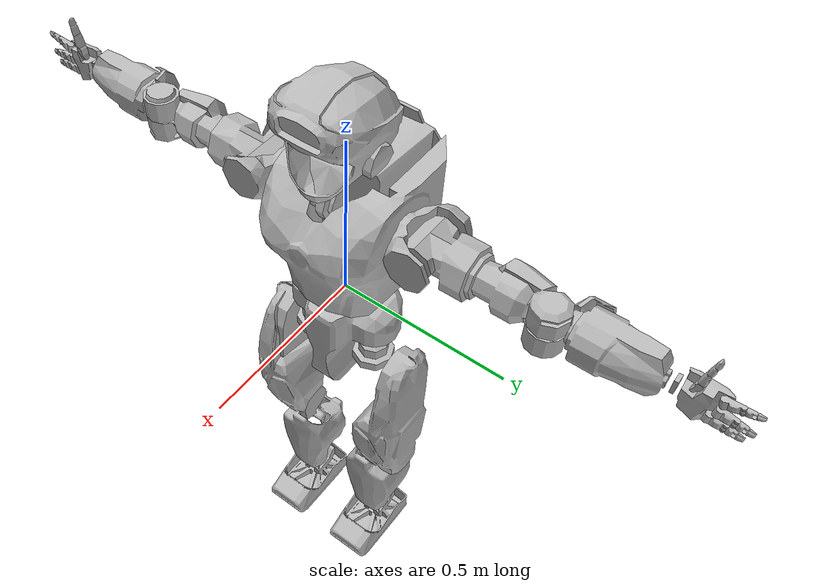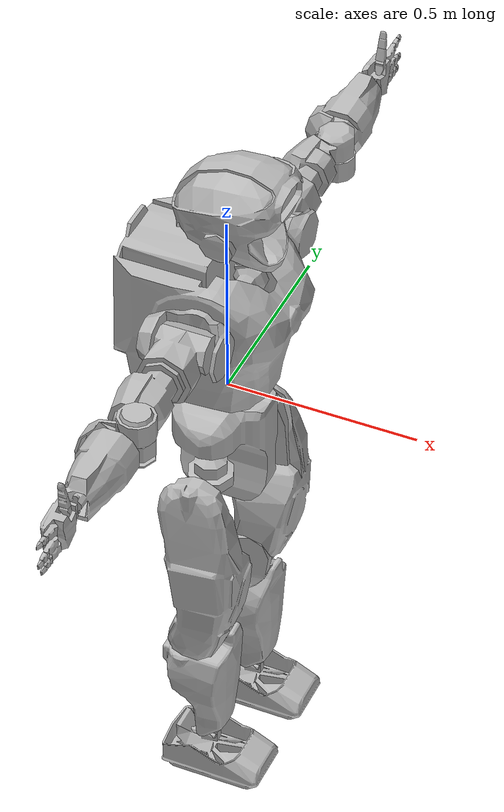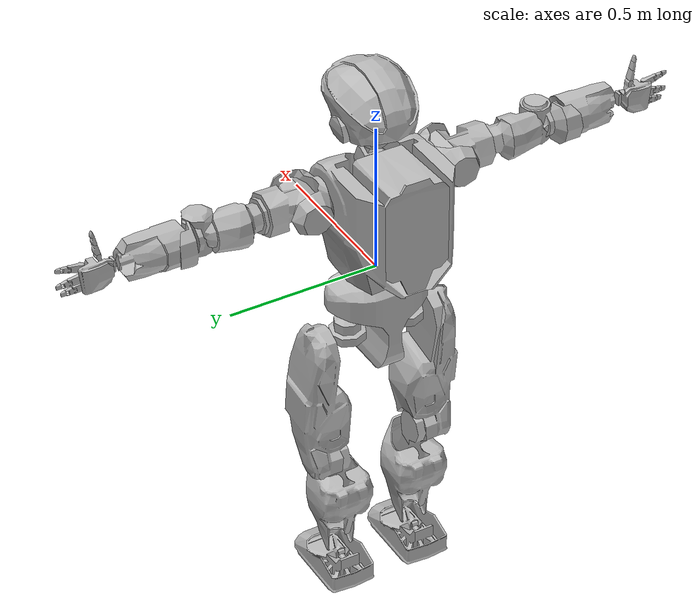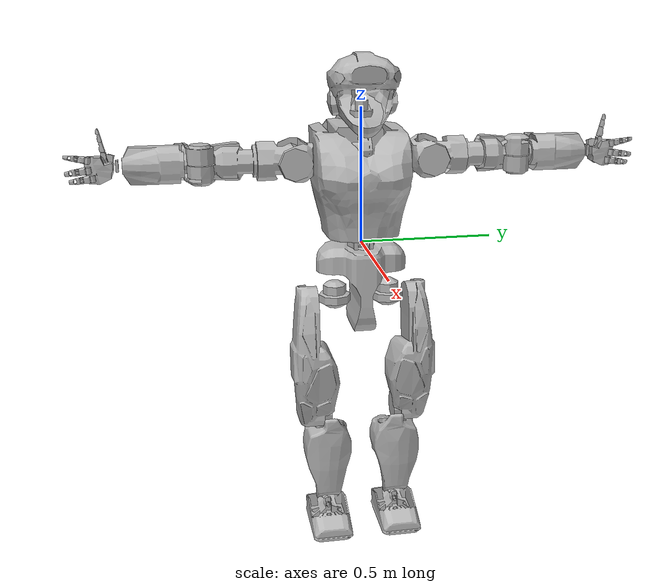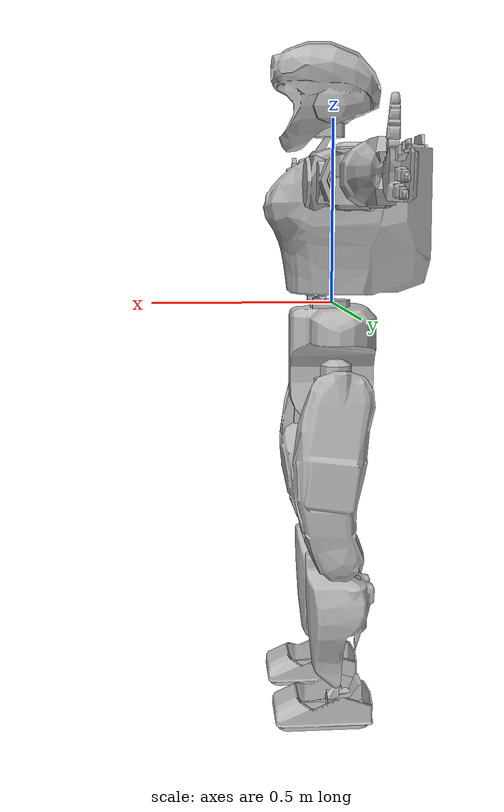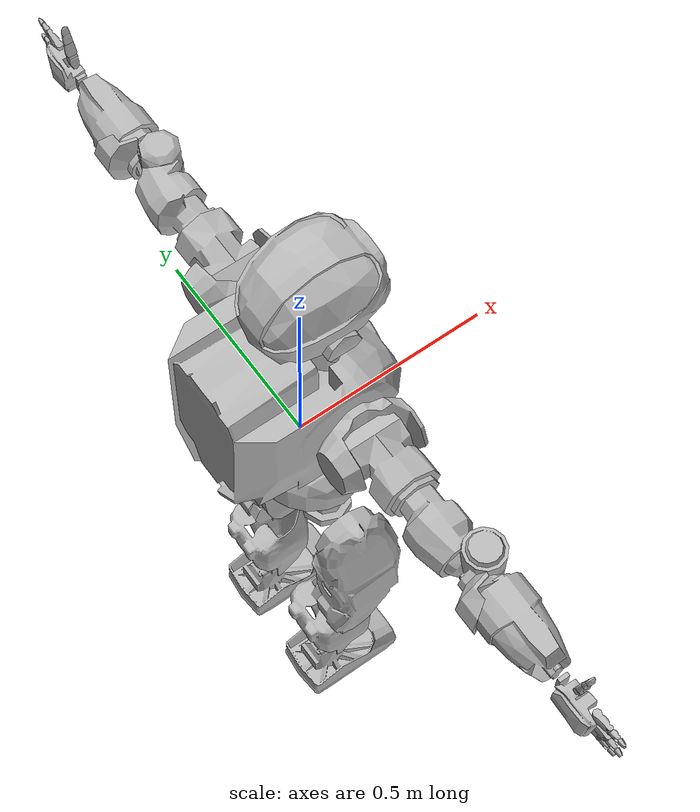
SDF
<sdf version='1.7'>
  <model name='valkyrie'>
    <link name='pelvis'>
      <inertial>
        <pose>-0.00532 -0.003512 -0.0036 0 -0 0</pose>
        <mass>8.22</mass>
        <inertia>
          <ixx>0.118664</ixx>
          <ixy>-0.000143482</ixy>
          <ixz>0.00327129</ixz>
          <iyy>0.0979634</iyy>
          <iyz>0.00215955</iyz>
          <izz>0.0838546</izz>
        </inertia>
      </inertial>
      <collision name='pelvis_collision'>
        <pose>0 0 0 0 -0 0</pose>
        <geometry>
          <mesh>
            <scale>1 1 1</scale>
            <uri>meshes/pelvis/pelvis.dae</uri>
          </mesh>
        </geometry>
      </collision>
      <visual name='pelvis_visual'>
        <pose>0 0 0 0 -0 0</pose>
        <geometry>
          <mesh>
            <scale>1 1 1</scale>
            <uri>meshes/pelvis/pelvis.dae</uri>
          </mesh>
        </geometry>
      </visual>
      <sensor name='pelvisMiddleImu' type='imu'>
        <always_on>1</always_on>
        <imu>
          <noise>
            <type>gaussian</type>
            <rate>
              <mean>0</mean>
              <stddev>0.0002</stddev>
              <bias_mean>7.5e-06</bias_mean>
              <bias_stddev>8e-07</bias_stddev>
            </rate>
            <accel>
              <mean>0</mean>
              <stddev>0.017</stddev>
              <bias_mean>0.1</bias_mean>
              <bias_stddev>0.001</bias_stddev>
            </accel>
          </noise>
        </imu>
        <pose>0 0 -0.108196 3.14159 -0 0</pose>
        <imuTransform>0.0 0.0 -0.10819638 3.14159 0.0 0.0</imuTransform>
      </sensor>
      <sensor name='pelvisRearImu' type='imu'>
        <always_on>1</always_on>
        <imu>
          <noise>
            <type>gaussian</type>
            <rate>
              <mean>0</mean>
              <stddev>0.0002</stddev>
              <bias_mean>7.5e-06</bias_mean>
              <bias_stddev>8e-07</bias_stddev>
            </rate>
            <accel>
              <mean>0</mean>
              <stddev>0.017</stddev>
              <bias_mean>0.1</bias_mean>
              <bias_stddev>0.001</bias_stddev>
            </accel>
          </noise>
        </imu>
        <pose>-0.075845 0 -0.111056 -3.14159 0.476467 -3.14159</pose>
        <imuTransform>-0.075844901 0.0 -0.111056426 -3.14159 0.476467 -3.14159</imuTransform>
        <node name='/sensors/rearPelvisIMU'/>
        <api name='imu_3dm_gx4_15_sensor::Imu3DmGx415Sensor'/>
        <port name='/dev/serial/by-id/usb-Lord_Microstrain_Lord_Inertial_Sensor_0000__6233.47095-if00'/>
      </sensor>
    </link>
    <joint name='leftHipYaw' type='revolute'>
      <pose relative_to='pelvis'>0 0.1016 -0.1853 0 -0 0</pose>
      <parent>pelvis</parent>
      <child>leftHipYawLink</child>
      <axis>
        <xyz>0 0 1</xyz>
        <limit>
          <lower>-0.4141</lower>
          <upper>1.1</upper>
          <effort>190</effort>
          <velocity>5.89</velocity>
        </limit>
        <dynamics>
          <damping>0.1</damping>
          <friction>0</friction>
          <spring_reference>0</spring_reference>
          <spring_stiffness>0</spring_stiffness>
        </dynamics>
      </axis>
      <physics>
        <provide_feedback>1</provide_feedback>
        <ode>
          <implicit_spring_damper>1</implicit_spring_damper>
          <cfm_damping>1</cfm_damping>
          <limit>
            <cfm>0</cfm>
            <erp>0.2</erp>
          </limit>
          <provide_feedback>1</provide_feedback>
        </ode>
      </physics>
    </joint>
    <link name='leftHipYawLink'>
      <pose relative_to='leftHipYaw'>0 0 0 0 -0 0</pose>
      <inertial>
        <pose>0.02176 -0.00131 0.03867 0 -0 0</pose>
        <mass>2.39</mass>
        <inertia>
          <ixx>0.017261</ixx>
          <ixy>0</ixy>
          <ixz>0</ixz>
          <iyy>0.0148662</iyy>
          <iyz>0</iyz>
          <izz>0.0112382</izz>
        </inertia>
      </inertial>
      <collision name='leftHipYawLink_collision'>
        <pose>0 0 0 0 -0 0</pose>
        <geometry>
          <mesh>
            <scale>1 1 1</scale>
            <uri>meshes/legs/lj1_left.dae</uri>
          </mesh>
        </geometry>
      </collision>
      <visual name='leftHipYawLink_visual'>
        <pose>0 0 0 0 -0 0</pose>
        <geometry>
          <mesh>
            <scale>1 1 1</scale>
            <uri>meshes/legs/lj1_left.dae</uri>
          </mesh>
        </geometry>
      </visual>
    </link>
    <joint name='leftHipRoll' type='revolute'>
      <pose relative_to='leftHipYawLink'>0 0 0 0 -0 0</pose>
      <parent>leftHipYawLink</parent>
      <child>leftHipRollLink</child>
      <axis>
        <xyz>1 0 0</xyz>
        <limit>
          <lower>-0.467</lower>
          <upper>0.5515</upper>
          <effort>350</effort>
          <velocity>7</velocity>
        </limit>
        <dynamics>
          <damping>0.1</damping>
          <friction>0</friction>
          <spring_reference>0</spring_reference>
          <spring_stiffness>0</spring_stiffness>
        </dynamics>
      </axis>
      <physics>
        <provide_feedback>1</provide_feedback>
        <ode>
          <implicit_spring_damper>1</implicit_spring_damper>
          <cfm_damping>1</cfm_damping>
          <limit>
            <cfm>0</cfm>
            <erp>0.2</erp>
          </limit>
          <provide_feedback>1</provide_feedback>
        </ode>
      </physics>
    </joint>
    <link name='leftHipRollLink'>
      <pose relative_to='leftHipRoll'>0 0 0 0 -0 0</pose>
      <inertial>
        <pose>0.012959 0.00755 -0.01595 0 -0 0</pose>
        <mass>3.665</mass>
        <inertia>
          <ixx>0.00597896</ixx>
          <ixy>-0.000234823</ixy>
          <ixz>0.000553962</ixz>
          <iyy>0.00937265</iyy>
          <iyz>0.000778956</iyz>
          <izz>0.00819312</izz>
        </inertia>
      </inertial>
    </link>
    <joint name='leftHipPitch' type='revolute'>
      <pose relative_to='leftHipRollLink'>0 0 -0.0609 0 -0 0</pose>
      <parent>leftHipRollLink</parent>
      <child>leftHipPitchLink</child>
      <axis>
        <xyz>0 1 0</xyz>
        <limit>
          <lower>-2.42</lower>
          <upper>1.619</upper>
          <effort>350</effort>
          <velocity>6.11</velocity>
        </limit>
        <dynamics>
          <damping>0.1</damping>
          <friction>0</friction>
          <spring_reference>0</spring_reference>
          <spring_stiffness>0</spring_stiffness>
        </dynamics>
      </axis>
      <physics>
        <provide_feedback>1</provide_feedback>
        <ode>
          <implicit_spring_damper>1</implicit_spring_damper>
          <cfm_damping>1</cfm_damping>
          <limit>
            <cfm>0</cfm>
            <erp>0.2</erp>
          </limit>
          <provide_feedback>1</provide_feedback>
        </ode>
      </physics>
    </joint>
    <link name='leftHipPitchLink'>
      <pose relative_to='leftHipPitch'>0 0 0 0 -0 0</pose>
      <inertial>
        <pose>0.016691 0.091397 -0.207875 0 -0 0</pose>
        <mass>10.2</mass>
        <inertia>
          <ixx>0.240834</ixx>
          <ixy>3.5915e-05</ixy>
          <ixz>0.00369938</ixz>
          <iyy>0.256897</iyy>
          <iyz>-0.001333</iyz>
          <izz>0.0232764</izz>
        </inertia>
      </inertial>
      <collision name='leftHipPitchLink_collision'>
        <pose>0 0 0 0 -0 0</pose>
        <geometry>
          <mesh>
            <scale>1 1 1</scale>
            <uri>meshes/legs/lj3_left.dae</uri>
          </mesh>
        </geometry>
      </collision>
      <visual name='leftHipPitchLink_visual'>
        <pose>0 0 0 0 -0 0</pose>
        <geometry>
          <mesh>
            <scale>1 1 1</scale>
            <uri>meshes/legs/lj3_left.dae</uri>
          </mesh>
        </geometry>
      </visual>
    </link>
    <joint name='leftKneePitch' type='revolute'>
      <pose relative_to='leftHipPitchLink'>0.000112 0.036105 -0.430959 0 -0 0</pose>
      <parent>leftHipPitchLink</parent>
      <child>leftKneePitchLink</child>
      <axis>
        <xyz>0 1 0</xyz>
        <limit>
          <lower>-0.083</lower>
          <upper>2.057</upper>
          <effort>350</effort>
          <velocity>6.11</velocity>
        </limit>
        <dynamics>
          <damping>0.1</damping>
          <friction>0</friction>
          <spring_reference>0</spring_reference>
          <spring_stiffness>0</spring_stiffness>
        </dynamics>
      </axis>
      <physics>
        <provide_feedback>1</provide_feedback>
        <ode>
          <implicit_spring_damper>1</implicit_spring_damper>
          <cfm_damping>1</cfm_damping>
          <limit>
            <cfm>0</cfm>
            <erp>0.2</erp>
          </limit>
          <provide_feedback>1</provide_feedback>
        </ode>
      </physics>
    </joint>
    <link name='leftKneePitchLink'>
      <pose relative_to='leftKneePitch'>0 0 0 0 -0 0</pose>
      <inertial>
        <pose>-0.022183 0.001703 -0.189418 0 -0 0</pose>
        <mass>6.2</mass>
        <inertia>
          <ixx>0.0869357</ixx>
          <ixy>9.929e-05</ixy>
          <ixz>0.000573207</ixz>
          <iyy>0.0915841</iyy>
          <iyz>0.000313745</iyz>
          <izz>0.0140173</izz>
        </inertia>
      </inertial>
      <collision name='leftKneePitchLink_collision'>
        <pose>0 0 0 0 -0 0</pose>
        <geometry>
          <mesh>
            <scale>1 1 1</scale>
            <uri>meshes/legs/lj4_left.dae</uri>
          </mesh>
        </geometry>
      </collision>
      <visual name='leftKneePitchLink_visual'>
        <pose>0 0 0 0 -0 0</pose>
        <geometry>
          <mesh>
            <scale>1 1 1</scale>
            <uri>meshes/legs/lj4_left.dae</uri>
          </mesh>
        </geometry>
      </visual>
    </link>
    <joint name='leftAnklePitch' type='revolute'>
      <pose relative_to='leftKneePitchLink'>-0.010238 0 -0.40627 0 -0 0</pose>
      <parent>leftKneePitchLink</parent>
      <child>leftAnklePitchLink</child>
      <axis>
        <xyz>0 1 0</xyz>
        <limit>
          <lower>-0.93</lower>
          <upper>0.65</upper>
          <effort>205</effort>
          <velocity>11</velocity>
        </limit>
        <dynamics>
          <damping>0.1</damping>
          <friction>0</friction>
          <spring_reference>0</spring_reference>
          <spring_stiffness>0</spring_stiffness>
        </dynamics>
      </axis>
      <physics>
        <provide_feedback>1</provide_feedback>
        <ode>
          <implicit_spring_damper>1</implicit_spring_damper>
          <cfm_damping>1</cfm_damping>
          <limit>
            <cfm>0</cfm>
            <erp>0.2</erp>
          </limit>
          <provide_feedback>1</provide_feedback>
        </ode>
      </physics>
    </joint>
    <link name='leftAnklePitchLink'>
      <pose relative_to='leftAnklePitch'>0 0 0 0 -0 0</pose>
      <inertial>
        <pose>0 0 0 0 -0 0</pose>
        <mass>0.03</mass>
        <inertia>
          <ixx>4.377e-06</ixx>
          <ixy>0</ixy>
          <ixz>0</ixz>
          <iyy>4.322e-06</iyy>
          <iyz>0</iyz>
          <izz>7.015e-06</izz>
        </inertia>
      </inertial>
      <collision name='leftAnklePitchLink_collision'>
        <pose>0 0 0 0 -0 0</pose>
        <geometry>
          <mesh>
            <scale>1 1 1</scale>
            <uri>meshes/legs/lj5.dae</uri>
          </mesh>
        </geometry>
      </collision>
      <visual name='leftAnklePitchLink_visual'>
        <pose>0 0 0 0 -0 0</pose>
        <geometry>
          <mesh>
            <scale>1 1 1</scale>
            <uri>meshes/legs/lj5.dae</uri>
          </mesh>
        </geometry>
      </visual>
    </link>
    <joint name='leftAnkleRoll' type='revolute'>
      <pose relative_to='leftAnklePitchLink'>0 0 0 0 -0 0</pose>
      <parent>leftAnklePitchLink</parent>
      <child>leftFoot</child>
      <axis>
        <xyz>1 0 0</xyz>
        <limit>
          <lower>-0.4</lower>
          <upper>0.4</upper>
          <effort>205</effort>
          <velocity>11</velocity>
        </limit>
        <dynamics>
          <damping>0.3</damping>
          <friction>0</friction>
          <spring_reference>0</spring_reference>
          <spring_stiffness>0</spring_stiffness>
        </dynamics>
      </axis>
      <physics>
        <provide_feedback>1</provide_feedback>
        <ode>
          <implicit_spring_damper>1</implicit_spring_damper>
          <cfm_damping>1</cfm_damping>
          <limit>
            <cfm>0</cfm>
            <erp>0.2</erp>
          </limit>
          <provide_feedback>1</provide_feedback>
        </ode>
      </physics>
      <sensor name='leftFootSixAxis' type='force_torque'>
        <pose>0.021565 0 -0.051054 3.14 -0 0</pose>
        <always_on>1</always_on>
        <update_rate>500</update_rate>
        <force_torque>
          <frame>sensor</frame>
          <measure_direction>parent_to_child</measure_direction>
        </force_torque>
        <sensor_number id='FT17218'/>
        <node id='/left_leg/ankle/left_actuator'/>
        <api name='ati_sensor_interface::ATISensorInterface'/>
      </sensor>
    </joint>
    <link name='leftFoot'>
      <pose relative_to='leftAnkleRoll'>0 0 0 0 -0 0</pose>
      <inertial>
        <pose>0.036909 0.004943 -0.048928 0 -0 0</pose>
        <mass>2.37</mass>
        <inertia>
          <ixx>0.00641532</ixx>
          <ixy>0.00020788</ixy>
          <ixz>0.00128536</ixz>
          <iyy>0.0179943</iyy>
          <iyz>-0.000202908</iyz>
          <izz>0.0209358</izz>
        </inertia>
      </inertial>
      <collision name='leftFoot_collision'>
        <pose>0.045 0 -0.056 0 -0 0</pose>
        <geometry>
          <box>
            <size>0.27 0.16 0.064</size>
          </box>
        </geometry>
        <surface>
          <contact>
            <ode>
              <kp>1e+06</kp>
              <kd>100</kd>
              <max_vel>1</max_vel>
              <min_depth>0</min_depth>
            </ode>
          </contact>
          <friction>
            <ode>
              <mu>1.5</mu>
              <mu2>1.5</mu2>
              <fdir1>1 0 0</fdir1>
            </ode>
          </friction>
        </surface>
      </collision>
      <visual name='leftFoot_visual'>
        <pose>0 0 0 0 -0 0</pose>
        <geometry>
          <mesh>
            <scale>1 1 1</scale>
            <uri>meshes/legs/foot.dae</uri>
          </mesh>
        </geometry>
      </visual>
    </link>
    <joint name='rightHipYaw' type='revolute'>
      <pose relative_to='pelvis'>0 -0.1016 -0.1853 0 -0 0</pose>
      <parent>pelvis</parent>
      <child>rightHipYawLink</child>
      <axis>
        <xyz>0 0 1</xyz>
        <limit>
          <lower>-1.1</lower>
          <upper>0.4141</upper>
          <effort>190</effort>
          <velocity>5.89</velocity>
        </limit>
        <dynamics>
          <damping>0.1</damping>
          <friction>0</friction>
          <spring_reference>0</spring_reference>
          <spring_stiffness>0</spring_stiffness>
        </dynamics>
      </axis>
      <physics>
        <provide_feedback>1</provide_feedback>
        <ode>
          <implicit_spring_damper>1</implicit_spring_damper>
          <cfm_damping>1</cfm_damping>
          <limit>
            <cfm>0</cfm>
            <erp>0.2</erp>
          </limit>
          <provide_feedback>1</provide_feedback>
        </ode>
      </physics>
    </joint>
    <link name='rightHipYawLink'>
      <pose relative_to='rightHipYaw'>0 0 0 0 -0 0</pose>
      <inertial>
        <pose>0.02176 0.00131 0.03867 0 -0 0</pose>
        <mass>2.39</mass>
        <inertia>
          <ixx>0.017261</ixx>
          <ixy>0</ixy>
          <ixz>0</ixz>
          <iyy>0.0148662</iyy>
          <iyz>0</iyz>
          <izz>0.0112382</izz>
        </inertia>
      </inertial>
      <collision name='rightHipYawLink_collision'>
        <pose>0 0 0 0 -0 0</pose>
        <geometry>
          <mesh>
            <scale>1 1 1</scale>
            <uri>meshes/legs/lj1_right.dae</uri>
          </mesh>
        </geometry>
      </collision>
      <visual name='rightHipYawLink_visual'>
        <pose>0 0 0 0 -0 0</pose>
        <geometry>
          <mesh>
            <scale>1 1 1</scale>
            <uri>meshes/legs/lj1_right.dae</uri>
          </mesh>
        </geometry>
      </visual>
    </link>
    <joint name='rightHipRoll' type='revolute'>
      <pose relative_to='rightHipYawLink'>0 0 0 0 -0 0</pose>
      <parent>rightHipYawLink</parent>
      <child>rightHipRollLink</child>
      <axis>
        <xyz>1 0 0</xyz>
        <limit>
          <lower>-0.5515</lower>
          <upper>0.467</upper>
          <effort>350</effort>
          <velocity>7</velocity>
        </limit>
        <dynamics>
          <damping>0.1</damping>
          <friction>0</friction>
          <spring_reference>0</spring_reference>
          <spring_stiffness>0</spring_stiffness>
        </dynamics>
      </axis>
      <physics>
        <provide_feedback>1</provide_feedback>
        <ode>
          <implicit_spring_damper>1</implicit_spring_damper>
          <cfm_damping>1</cfm_damping>
          <limit>
            <cfm>0</cfm>
            <erp>0.2</erp>
          </limit>
          <provide_feedback>1</provide_feedback>
        </ode>
      </physics>
    </joint>
    <link name='rightHipRollLink'>
      <pose relative_to='rightHipRoll'>0 0 0 0 -0 0</pose>
      <inertial>
        <pose>0.012959 -0.00755 -0.01595 0 -0 0</pose>
        <mass>3.665</mass>
        <inertia>
          <ixx>0.00597896</ixx>
          <ixy>0.000234823</ixy>
          <ixz>0.000553962</ixz>
          <iyy>0.00937265</iyy>
          <iyz>-0.000778956</iyz>
          <izz>0.00819312</izz>
        </inertia>
      </inertial>
    </link>
    <joint name='rightHipPitch' type='revolute'>
      <pose relative_to='rightHipRollLink'>0 0 -0.0609 0 -0 0</pose>
      <parent>rightHipRollLink</parent>
      <child>rightHipPitchLink</child>
      <axis>
        <xyz>0 1 0</xyz>
        <limit>
          <lower>-2.42</lower>
          <upper>1.619</upper>
          <effort>350</effort>
          <velocity>6.11</velocity>
        </limit>
        <dynamics>
          <damping>0.1</damping>
          <friction>0</friction>
          <spring_reference>0</spring_reference>
          <spring_stiffness>0</spring_stiffness>
        </dynamics>
      </axis>
      <physics>
        <provide_feedback>1</provide_feedback>
        <ode>
          <implicit_spring_damper>1</implicit_spring_damper>
          <cfm_damping>1</cfm_damping>
          <limit>
            <cfm>0</cfm>
            <erp>0.2</erp>
          </limit>
          <provide_feedback>1</provide_feedback>
        </ode>
      </physics>
    </joint>
    <link name='rightHipPitchLink'>
      <pose relative_to='rightHipPitch'>0 0 0 0 -0 0</pose>
      <inertial>
        <pose>0.016691 -0.091397 -0.207875 0 -0 0</pose>
        <mass>10.2</mass>
        <inertia>
          <ixx>0.240834</ixx>
          <ixy>-3.5915e-05</ixy>
          <ixz>0.00369938</ixz>
          <iyy>0.256897</iyy>
          <iyz>0.001333</iyz>
          <izz>0.0232764</izz>
        </inertia>
      </inertial>
      <collision name='rightHipPitchLink_collision'>
        <pose>0 0 0 0 -0 0</pose>
        <geometry>
          <mesh>
            <scale>1 1 1</scale>
            <uri>meshes/legs/lj3_right.dae</uri>
          </mesh>
        </geometry>
      </collision>
      <visual name='rightHipPitchLink_visual'>
        <pose>0 0 0 0 -0 0</pose>
        <geometry>
          <mesh>
            <scale>1 1 1</scale>
            <uri>meshes/legs/lj3_right.dae</uri>
          </mesh>
        </geometry>
      </visual>
    </link>
    <joint name='rightKneePitch' type='revolute'>
      <pose relative_to='rightHipPitchLink'>0.000112 -0.036105 -0.430959 0 -0 0</pose>
      <parent>rightHipPitchLink</parent>
      <child>rightKneePitchLink</child>
      <axis>
        <xyz>0 1 0</xyz>
        <limit>
          <lower>-0.083</lower>
          <upper>2.057</upper>
          <effort>350</effort>
          <velocity>6.11</velocity>
        </limit>
        <dynamics>
          <damping>0.1</damping>
          <friction>0</friction>
          <spring_reference>0</spring_reference>
          <spring_stiffness>0</spring_stiffness>
        </dynamics>
      </axis>
      <physics>
        <provide_feedback>1</provide_feedback>
        <ode>
          <implicit_spring_damper>1</implicit_spring_damper>
          <cfm_damping>1</cfm_damping>
          <limit>
            <cfm>0</cfm>
            <erp>0.2</erp>
          </limit>
          <provide_feedback>1</provide_feedback>
        </ode>
      </physics>
    </joint>
    <link name='rightKneePitchLink'>
      <pose relative_to='rightKneePitch'>0 0 0 0 -0 0</pose>
      <inertial>
        <pose>-0.022183 0.001703 -0.189418 0 -0 0</pose>
        <mass>6.2</mass>
        <inertia>
          <ixx>0.0869357</ixx>
          <ixy>9.929e-05</ixy>
          <ixz>0.000573207</ixz>
          <iyy>0.0915841</iyy>
          <iyz>0.000313745</iyz>
          <izz>0.0140173</izz>
        </inertia>
      </inertial>
      <collision name='rightKneePitchLink_collision'>
        <pose>0 0 0 0 -0 0</pose>
        <geometry>
          <mesh>
            <scale>1 1 1</scale>
            <uri>meshes/legs/lj4_right.dae</uri>
          </mesh>
        </geometry>
      </collision>
      <visual name='rightKneePitchLink_visual'>
        <pose>0 0 0 0 -0 0</pose>
        <geometry>
          <mesh>
            <scale>1 1 1</scale>
            <uri>meshes/legs/lj4_right.dae</uri>
          </mesh>
        </geometry>
      </visual>
    </link>
    <joint name='rightAnklePitch' type='revolute'>
      <pose relative_to='rightKneePitchLink'>-0.010238 0 -0.40627 0 -0 0</pose>
      <parent>rightKneePitchLink</parent>
      <child>rightAnklePitchLink</child>
      <axis>
        <xyz>0 1 0</xyz>
        <limit>
          <lower>-0.93</lower>
          <upper>0.65</upper>
          <effort>205</effort>
          <velocity>11</velocity>
        </limit>
        <dynamics>
          <damping>0.1</damping>
          <friction>0</friction>
          <spring_reference>0</spring_reference>
          <spring_stiffness>0</spring_stiffness>
        </dynamics>
      </axis>
      <physics>
        <provide_feedback>1</provide_feedback>
        <ode>
          <implicit_spring_damper>1</implicit_spring_damper>
          <cfm_damping>1</cfm_damping>
          <limit>
            <cfm>0</cfm>
            <erp>0.2</erp>
          </limit>
          <provide_feedback>1</provide_feedback>
        </ode>
      </physics>
    </joint>
    <link name='rightAnklePitchLink'>
      <pose relative_to='rightAnklePitch'>0 0 0 0 -0 0</pose>
      <inertial>
        <pose>0 0 0 0 -0 0</pose>
        <mass>0.03</mass>
        <inertia>
          <ixx>4.377e-06</ixx>
          <ixy>0</ixy>
          <ixz>0</ixz>
          <iyy>4.322e-06</iyy>
          <iyz>0</iyz>
          <izz>7.015e-06</izz>
        </inertia>
      </inertial>
      <collision name='rightAnklePitchLink_collision'>
        <pose>0 0 0 0 -0 0</pose>
        <geometry>
          <mesh>
            <scale>1 1 1</scale>
            <uri>meshes/legs/lj5.dae</uri>
          </mesh>
        </geometry>
      </collision>
      <visual name='rightAnklePitchLink_visual'>
        <pose>0 0 0 0 -0 0</pose>
        <geometry>
          <mesh>
            <scale>1 1 1</scale>
            <uri>meshes/legs/lj5.dae</uri>
          </mesh>
        </geometry>
      </visual>
    </link>
    <joint name='rightAnkleRoll' type='revolute'>
      <pose relative_to='rightAnklePitchLink'>0 0 0 0 -0 0</pose>
      <parent>rightAnklePitchLink</parent>
      <child>rightFoot</child>
      <axis>
        <xyz>1 0 0</xyz>
        <limit>
          <lower>-0.4</lower>
          <upper>0.4</upper>
          <effort>205</effort>
          <velocity>11</velocity>
        </limit>
        <dynamics>
          <damping>0.3</damping>
          <friction>0</friction>
          <spring_reference>0</spring_reference>
          <spring_stiffness>0</spring_stiffness>
        </dynamics>
      </axis>
      <physics>
        <provide_feedback>1</provide_feedback>
        <ode>
          <implicit_spring_damper>1</implicit_spring_damper>
          <cfm_damping>1</cfm_damping>
          <limit>
            <cfm>0</cfm>
            <erp>0.2</erp>
          </limit>
          <provide_feedback>1</provide_feedback>
        </ode>
      </physics>
      <sensor name='rightFootSixAxis' type='force_torque'>
        <pose>0.021565 0 -0.051054 3.14 -0 0</pose>
        <always_on>1</always_on>
        <update_rate>500</update_rate>
        <force_torque>
          <frame>sensor</frame>
          <measure_direction>parent_to_child</measure_direction>
        </force_torque>
        <sensor_number id='FT14018'/>
        <node id='/right_leg/ankle/left_actuator'/>
        <api name='ati_sensor_interface::ATISensorInterface'/>
      </sensor>
    </joint>
    <link name='rightFoot'>
      <pose relative_to='rightAnkleRoll'>0 0 0 0 -0 0</pose>
      <inertial>
        <pose>0.036909 0.004943 -0.048928 0 -0 0</pose>
        <mass>2.37</mass>
        <inertia>
          <ixx>0.00641532</ixx>
          <ixy>0.00020788</ixy>
          <ixz>0.00128536</ixz>
          <iyy>0.0179943</iyy>
          <iyz>-0.000202908</iyz>
          <izz>0.0209358</izz>
        </inertia>
      </inertial>
      <collision name='rightFoot_collision'>
        <pose>0.045 0 -0.056 0 -0 0</pose>
        <geometry>
          <box>
            <size>0.27 0.16 0.064</size>
          </box>
        </geometry>
        <surface>
          <contact>
            <ode>
              <kp>1e+06</kp>
              <kd>100</kd>
              <max_vel>1</max_vel>
              <min_depth>0</min_depth>
            </ode>
          </contact>
          <friction>
            <ode>
              <mu>1.5</mu>
              <mu2>1.5</mu2>
              <fdir1>1 0 0</fdir1>
            </ode>
          </friction>
        </surface>
      </collision>
      <visual name='rightFoot_visual'>
        <pose>0 0 0 0 -0 0</pose>
        <geometry>
          <mesh>
            <scale>1 1 1</scale>
            <uri>meshes/legs/foot.dae</uri>
          </mesh>
        </geometry>
      </visual>
    </link>
    <joint name='torsoYaw' type='revolute'>
      <pose relative_to='pelvis'>0 0 0 0 -0 0</pose>
      <parent>pelvis</parent>
      <child>torsoYawLink</child>
      <axis>
        <xyz>0 0 1</xyz>
        <limit>
          <lower>-1.329</lower>
          <upper>1.181</upper>
          <effort>190</effort>
          <velocity>5.89</velocity>
        </limit>
        <dynamics>
          <damping>0.1</damping>
          <friction>0</friction>
          <spring_reference>0</spring_reference>
          <spring_stiffness>0</spring_stiffness>
        </dynamics>
      </axis>
      <physics>
        <provide_feedback>1</provide_feedback>
        <ode>
          <implicit_spring_damper>1</implicit_spring_damper>
          <cfm_damping>1</cfm_damping>
          <limit>
            <cfm>0</cfm>
            <erp>0.2</erp>
          </limit>
          <provide_feedback>1</provide_feedback>
        </ode>
      </physics>
    </joint>
    <link name='torsoYawLink'>
      <pose relative_to='torsoYaw'>0 0 0 0 -0 0</pose>
      <inertial>
        <pose>0 0 -0.01 0 -0 0</pose>
        <mass>0.5</mass>
        <inertia>
          <ixx>0.000608427</ixx>
          <ixy>-1.172e-06</ixy>
          <ixz>1.647e-06</ixz>
          <iyy>0.000620328</iyy>
          <iyz>-2.33e-07</iyz>
          <izz>0.00107811</izz>
        </inertia>
      </inertial>
      <collision name='torsoYawLink_collision'>
        <pose>0 0 0 0 -0 0</pose>
        <geometry>
          <mesh>
            <scale>1 1 1</scale>
            <uri>meshes/torso/torsoyaw.dae</uri>
          </mesh>
        </geometry>
      </collision>
      <visual name='torsoYawLink_visual'>
        <pose>0 0 0 0 -0 0</pose>
        <geometry>
          <mesh>
            <scale>1 1 1</scale>
            <uri>meshes/torso/torsoyaw.dae</uri>
          </mesh>
        </geometry>
      </visual>
    </link>
    <joint name='torsoPitch' type='revolute'>
      <pose relative_to='torsoYawLink'>0.04191 0 0 0 -0 0</pose>
      <parent>torsoYawLink</parent>
      <child>torsoPitchLink</child>
      <axis>
        <xyz>0 1 0</xyz>
        <limit>
          <lower>-0.13</lower>
          <upper>0.666</upper>
          <effort>150</effort>
          <velocity>9</velocity>
        </limit>
        <dynamics>
          <damping>0.1</damping>
          <friction>0</friction>
          <spring_reference>0</spring_reference>
          <spring_stiffness>0</spring_stiffness>
        </dynamics>
      </axis>
      <physics>
        <provide_feedback>1</provide_feedback>
        <ode>
          <implicit_spring_damper>1</implicit_spring_damper>
          <cfm_damping>1</cfm_damping>
          <limit>
            <cfm>0</cfm>
            <erp>0.2</erp>
          </limit>
          <provide_feedback>1</provide_feedback>
        </ode>
      </physics>
    </joint>
    <link name='torsoPitchLink'>
      <pose relative_to='torsoPitch'>0 0 0 0 -0 0</pose>
      <inertial>
        <pose>0 0 0.005 0 -0 0</pose>
        <mass>0.1</mass>
        <inertia>
          <ixx>3.032e-05</ixx>
          <ixy>0</ixy>
          <ixz>-1.145e-06</ixz>
          <iyy>2.1274e-05</iyy>
          <iyz>0</iyz>
          <izz>2.8285e-05</izz>
        </inertia>
      </inertial>
      <collision name='torsoPitchLink_collision'>
        <pose>0 0 0 0 -0 0</pose>
        <geometry>
          <mesh>
            <scale>1 1 1</scale>
            <uri>meshes/torso/torsopitch.dae</uri>
          </mesh>
        </geometry>
      </collision>
      <visual name='torsoPitchLink_visual'>
        <pose>0 0 0 0 -0 0</pose>
        <geometry>
          <mesh>
            <scale>1 1 1</scale>
            <uri>meshes/torso/torsopitch.dae</uri>
          </mesh>
        </geometry>
      </visual>
    </link>
    <joint name='torsoRoll' type='revolute'>
      <pose relative_to='torsoPitchLink'>0 0 0.0203 0 -0 0</pose>
      <parent>torsoPitchLink</parent>
      <child>torso</child>
      <axis>
        <xyz>1 0 0</xyz>
        <limit>
          <lower>-0.23</lower>
          <upper>0.255</upper>
          <effort>150</effort>
          <velocity>9</velocity>
        </limit>
        <dynamics>
          <damping>0.1</damping>
          <friction>0</friction>
          <spring_reference>0</spring_reference>
          <spring_stiffness>0</spring_stiffness>
        </dynamics>
      </axis>
      <physics>
        <provide_feedback>1</provide_feedback>
        <ode>
          <implicit_spring_damper>1</implicit_spring_damper>
          <cfm_damping>1</cfm_damping>
          <limit>
            <cfm>0</cfm>
            <erp>0.2</erp>
          </limit>
          <provide_feedback>1</provide_feedback>
        </ode>
      </physics>
    </joint>
    <link name='torso'>
      <pose relative_to='torsoRoll'>0 0 0 0 -0 0</pose>
      <inertial>
        <pose>-0.095548 -0.003337 0.243098 0 -0 0</pose>
        <mass>39.47</mass>
        <inertia>
          <ixx>0.873269</ixx>
          <ixy>9.95625e-05</ixy>
          <ixz>0.0613452</ixz>
          <iyy>1.01085</iyy>
          <iyz>0.00181849</iyz>
          <izz>0.778398</izz>
        </inertia>
      </inertial>
      <collision name='torso_collision'>
        <pose>0 0 0 0 -0 0</pose>
        <geometry>
          <mesh>
            <scale>1 1 1</scale>
            <uri>meshes/torso/torso.dae</uri>
          </mesh>
        </geometry>
      </collision>
      <visual name='torso_visual'>
        <pose>0 0 0 0 -0 0</pose>
        <geometry>
          <mesh>
            <scale>1 1 1</scale>
            <uri>meshes/torso/torso.dae</uri>
          </mesh>
        </geometry>
      </visual>
      <sensor name='leftHazardCamera' type='camera'>
        <camera>
          <image>
            <width>1280</width>
            <height>1024</height>
            <format>R8G8B8</format>
          </image>
          <horizontal_fov>1.378</horizontal_fov>
          <clip>
            <near>0.1</near>
            <far>100</far>
          </clip>
        </camera>
        <update_rate>60</update_rate>
        <pose>0.0345 0.0406 0.1135 1.57 -0 1.57</pose>
      </sensor>
      <sensor name='leftTorsoImu' type='imu'>
        <always_on>1</always_on>
        <imu>
          <noise>
            <type>gaussian</type>
            <rate>
              <mean>0</mean>
              <stddev>0.0002</stddev>
              <bias_mean>7.5e-06</bias_mean>
              <bias_stddev>8e-07</bias_stddev>
            </rate>
            <accel>
              <mean>0</mean>
              <stddev>0.017</stddev>
              <bias_mean>0.1</bias_mean>
              <bias_stddev>0.001</bias_stddev>
            </accel>
          </noise>
        </imu>
        <pose>-0.062763 0.134239 0.363068 -1.5707 0 0</pose>
        <imuTransform>-0.0627634 0.134239 0.3630676 -1.5707 0.0 0.0</imuTransform>
        <node name='/sensors/leftTorsoIMU'/>
        <api name='imu_3dm_gx4_15_sensor::Imu3DmGx415Sensor'/>
        <port name='/dev/serial/by-id/usb-Lord_Microstrain_Lord_Inertial_Sensor_0000__6233.47090-if00'/>
      </sensor>
      <sensor name='rightHazardCamera' type='camera'>
        <camera>
          <image>
            <width>1280</width>
            <height>1024</height>
            <format>R8G8B8</format>
          </image>
          <horizontal_fov>1.378</horizontal_fov>
          <clip>
            <near>0.1</near>
            <far>100</far>
          </clip>
        </camera>
        <update_rate>60</update_rate>
        <pose>0.0345 -0.0406 0.1135 1.57 -0 1.57</pose>
      </sensor>
    </link>
    <joint name='leftShoulderPitch' type='revolute'>
      <pose relative_to='torso'>-0.0316 0 0.2984 0 -0 0</pose>
      <parent>torso</parent>
      <child>leftShoulderPitchLink</child>
      <axis>
        <xyz>0 1 0</xyz>
        <limit>
          <lower>-2.85</lower>
          <upper>2</upper>
          <effort>190</effort>
          <velocity>5.89</velocity>
        </limit>
        <dynamics>
          <damping>0.1</damping>
          <friction>0</friction>
          <spring_reference>0</spring_reference>
          <spring_stiffness>0</spring_stiffness>
        </dynamics>
      </axis>
      <physics>
        <provide_feedback>1</provide_feedback>
        <ode>
          <implicit_spring_damper>1</implicit_spring_damper>
          <cfm_damping>1</cfm_damping>
          <limit>
            <cfm>0</cfm>
            <erp>0.2</erp>
          </limit>
          <provide_feedback>1</provide_feedback>
        </ode>
      </physics>
    </joint>
    <link name='leftShoulderPitchLink'>
      <pose relative_to='leftShoulderPitch'>0 0 0 0 -0 0</pose>
      <inertial>
        <pose>-0.012 0.251 0 0 -0 0</pose>
        <mass>2.65</mass>
        <inertia>
          <ixx>0.0137182</ixx>
          <ixy>0</ixy>
          <ixz>0</ixz>
          <iyy>0.0105028</iyy>
          <iyz>0</iyz>
          <izz>0.0148064</izz>
        </inertia>
      </inertial>
      <collision name='leftShoulderPitchLink_collision'>
        <pose>0 0 0 0 -0 0</pose>
        <geometry>
          <mesh>
            <scale>1 1 1</scale>
            <uri>meshes/arms/aj1_left.dae</uri>
          </mesh>
        </geometry>
      </collision>
      <visual name='leftShoulderPitchLink_visual'>
        <pose>0 0 0 0 -0 0</pose>
        <geometry>
          <mesh>
            <scale>1 1 1</scale>
            <uri>meshes/arms/aj1_left.dae</uri>
          </mesh>
        </geometry>
      </visual>
    </link>
    <joint name='leftShoulderRoll' type='revolute'>
      <pose relative_to='leftShoulderPitchLink'>0 0.2499 0 0 -0 0</pose>
      <parent>leftShoulderPitchLink</parent>
      <child>leftShoulderRollLink</child>
      <axis>
        <xyz>1 0 0</xyz>
        <limit>
          <lower>-1.519</lower>
          <upper>1.266</upper>
          <effort>190</effort>
          <velocity>5.89</velocity>
        </limit>
        <dynamics>
          <damping>0.1</damping>
          <friction>0</friction>
          <spring_reference>0</spring_reference>
          <spring_stiffness>0</spring_stiffness>
        </dynamics>
      </axis>
      <physics>
        <provide_feedback>1</provide_feedback>
        <ode>
          <implicit_spring_damper>1</implicit_spring_damper>
          <cfm_damping>1</cfm_damping>
          <limit>
            <cfm>0</cfm>
            <erp>0.2</erp>
          </limit>
          <provide_feedback>1</provide_feedback>
        </ode>
      </physics>
    </joint>
    <link name='leftShoulderRollLink'>
      <pose relative_to='leftShoulderRoll'>0 0 0 0 -0 0</pose>
      <inertial>
        <pose>-0.008513 0.02068 -0.001088 0 -0 0</pose>
        <mass>3.97</mass>
        <inertia>
          <ixx>0.0145988</ixx>
          <ixy>-0.00066764</ixy>
          <ixz>-3.629e-05</ixz>
          <iyy>0.00645214</iyy>
          <iyz>-8.283e-05</iyz>
          <izz>0.0168483</izz>
        </inertia>
      </inertial>
      <collision name='leftShoulderRollLink_collision'>
        <pose>0 0 0 0 -0 0</pose>
        <geometry>
          <mesh>
            <scale>1 1 1</scale>
            <uri>meshes/arms/aj2_left.dae</uri>
          </mesh>
        </geometry>
      </collision>
      <visual name='leftShoulderRollLink_visual'>
        <pose>0 0 0 0 -0 0</pose>
        <geometry>
          <mesh>
            <scale>1 1 1</scale>
            <uri>meshes/arms/aj2_left.dae</uri>
          </mesh>
        </geometry>
      </visual>
    </link>
    <joint name='leftShoulderYaw' type='revolute'>
      <pose relative_to='leftShoulderRollLink'>0 0 0 0 -0 0</pose>
      <parent>leftShoulderRollLink</parent>
      <child>leftShoulderYawLink</child>
      <axis>
        <xyz>0 1 0</xyz>
        <limit>
          <lower>-3.1</lower>
          <upper>2.18</upper>
          <effort>65</effort>
          <velocity>11.5</velocity>
        </limit>
        <dynamics>
          <damping>0.1</damping>
          <friction>0</friction>
          <spring_reference>0</spring_reference>
          <spring_stiffness>0</spring_stiffness>
        </dynamics>
      </axis>
      <physics>
        <provide_feedback>1</provide_feedback>
        <ode>
          <implicit_spring_damper>1</implicit_spring_damper>
          <cfm_damping>1</cfm_damping>
          <limit>
            <cfm>0</cfm>
            <erp>0.2</erp>
          </limit>
          <provide_feedback>1</provide_feedback>
        </ode>
      </physics>
    </joint>
    <link name='leftShoulderYawLink'>
      <pose relative_to='leftShoulderYaw'>0 0 0 0 -0 0</pose>
      <inertial>
        <pose>-0.004304 0.209832 0.007295 0 -0 0</pose>
        <mass>3.085</mass>
        <inertia>
          <ixx>0.0393552</ixx>
          <ixy>-0.00782708</ixy>
          <ixz>-0.000753947</ixz>
          <iyy>0.00490577</iyy>
          <iyz>0.00272387</iyz>
          <izz>0.0418795</izz>
        </inertia>
      </inertial>
      <collision name='leftShoulderYawLink_collision'>
        <pose>0 0 0 0 -0 0</pose>
        <geometry>
          <mesh>
            <scale>1 1 1</scale>
            <uri>meshes/arms/aj3_left.dae</uri>
          </mesh>
        </geometry>
      </collision>
      <visual name='leftShoulderYawLink_visual'>
        <pose>0 0 0 0 -0 0</pose>
        <geometry>
          <mesh>
            <scale>1 1 1</scale>
            <uri>meshes/arms/aj3_left.dae</uri>
          </mesh>
        </geometry>
      </visual>
    </link>
    <joint name='leftElbowPitch' type='revolute'>
      <pose relative_to='leftShoulderYawLink'>0.0254 0.33 0 0 -0 0</pose>
      <parent>leftShoulderYawLink</parent>
      <child>leftElbowPitchLink</child>
      <axis>
        <xyz>0 0 1</xyz>
        <limit>
          <lower>-2.174</lower>
          <upper>0.12</upper>
          <effort>65</effort>
          <velocity>11.5</velocity>
        </limit>
        <dynamics>
          <damping>0.1</damping>
          <friction>0</friction>
          <spring_reference>0</spring_reference>
          <spring_stiffness>0</spring_stiffness>
        </dynamics>
      </axis>
      <physics>
        <provide_feedback>1</provide_feedback>
        <ode>
          <implicit_spring_damper>1</implicit_spring_damper>
          <cfm_damping>1</cfm_damping>
          <limit>
            <cfm>0</cfm>
            <erp>0.2</erp>
          </limit>
          <provide_feedback>1</provide_feedback>
        </ode>
      </physics>
    </joint>
    <link name='leftElbowPitchLink'>
      <pose relative_to='leftElbowPitch'>0 0 0 0 -0 0</pose>
      <inertial>
        <pose>-0.020344 0.014722 0.0223 0 -0 0</pose>
        <mass>1.83</mass>
        <inertia>
          <ixx>0.00331452</ixx>
          <ixy>0.000535099</ixy>
          <ixz>0.000728077</ixz>
          <iyy>0.00350567</iyy>
          <iyz>-0.000423865</iyz>
          <izz>0.00301128</izz>
        </inertia>
      </inertial>
      <collision name='leftElbowPitchLink_collision'>
        <pose>0 0 0 0 -0 0</pose>
        <geometry>
          <mesh>
            <scale>1 1 1</scale>
            <uri>meshes/arms/aj4_left.dae</uri>
          </mesh>
        </geometry>
      </collision>
      <visual name='leftElbowPitchLink_visual'>
        <pose>0 0 0 0 -0 0</pose>
        <geometry>
          <mesh>
            <scale>1 1 1</scale>
            <uri>meshes/arms/aj4_left.dae</uri>
          </mesh>
        </geometry>
      </visual>
    </link>
    <joint name='leftForearmYaw' type='revolute'>
      <pose relative_to='leftElbowPitchLink'>-0.0254 0 0 0 -0 0</pose>
      <parent>leftElbowPitchLink</parent>
      <child>leftForearmLink</child>
      <axis>
        <xyz>0 1 0</xyz>
        <limit>
          <lower>-2.019</lower>
          <upper>3.14</upper>
          <effort>26</effort>
          <velocity>5</velocity>
        </limit>
        <dynamics>
          <damping>0.1</damping>
          <friction>0</friction>
          <spring_reference>0</spring_reference>
          <spring_stiffness>0</spring_stiffness>
        </dynamics>
      </axis>
      <physics>
        <provide_feedback>1</provide_feedback>
        <ode>
          <implicit_spring_damper>1</implicit_spring_damper>
          <cfm_damping>1</cfm_damping>
          <limit>
            <cfm>0</cfm>
            <erp>0.2</erp>
          </limit>
          <provide_feedback>1</provide_feedback>
        </ode>
      </physics>
    </joint>
    <link name='leftForearmLink'>
      <pose relative_to='leftForearmYaw'>0 0 0 0 -0 0</pose>
      <inertial>
        <pose>0.015 0.13 0.019564 0 -0 0</pose>
        <mass>2.476</mass>
        <inertia>
          <ixx>0.0117554</ixx>
          <ixy>0.00130085</ixy>
          <ixz>-0.000727141</ixz>
          <iyy>0.00507157</iyy>
          <iyz>0.00169542</iyz>
          <izz>0.0113657</izz>
        </inertia>
      </inertial>
      <collision name='leftForearmLink_collision'>
        <pose>0 0 0 0 -0 0</pose>
        <geometry>
          <mesh>
            <scale>1 1 1</scale>
            <uri>meshes/arms/aj5_left.dae</uri>
          </mesh>
        </geometry>
      </collision>
      <visual name='leftForearmLink_visual'>
        <pose>0 0 0 0 -0 0</pose>
        <geometry>
          <mesh>
            <scale>1 1 1</scale>
            <uri>meshes/arms/aj5_left.dae</uri>
          </mesh>
        </geometry>
      </visual>
    </link>
    <joint name='leftWristRoll' type='revolute'>
      <pose relative_to='leftForearmLink'>0 0.2871 0 0 -0 0</pose>
      <parent>leftForearmLink</parent>
      <child>leftWristRollLink</child>
      <axis>
        <xyz>1 0 0</xyz>
        <limit>
          <lower>-0.62</lower>
          <upper>0.625</upper>
          <effort>14</effort>
          <velocity>1</velocity>
        </limit>
        <dynamics>
          <damping>0.1</damping>
          <friction>0</friction>
          <spring_reference>0</spring_reference>
          <spring_stiffness>0</spring_stiffness>
        </dynamics>
      </axis>
      <physics>
        <provide_feedback>1</provide_feedback>
        <ode>
          <implicit_spring_damper>1</implicit_spring_damper>
          <cfm_damping>1</cfm_damping>
          <limit>
            <cfm>0</cfm>
            <erp>0.2</erp>
          </limit>
          <provide_feedback>1</provide_feedback>
        </ode>
      </physics>
    </joint>
    <link name='leftWristRollLink'>
      <pose relative_to='leftWristRoll'>0 0 0 0 -0 0</pose>
      <inertial>
        <pose>0 0 0 0 -0 0</pose>
        <mass>0.14</mass>
        <inertia>
          <ixx>3.0251e-05</ixx>
          <ixy>1.25e-07</ixy>
          <ixz>3.6e-08</ixz>
          <iyy>3.772e-05</iyy>
          <iyz>0</iyz>
          <izz>9.395e-06</izz>
        </inertia>
      </inertial>
      <collision name='leftWristRollLink_collision'>
        <pose>0 0 0 0 -0 0</pose>
        <geometry>
          <mesh>
            <scale>1 1 1</scale>
            <uri>meshes/arms/aj6_left.dae</uri>
          </mesh>
        </geometry>
      </collision>
      <visual name='leftWristRollLink_visual'>
        <pose>0 0 0 0 -0 0</pose>
        <geometry>
          <mesh>
            <scale>1 1 1</scale>
            <uri>meshes/arms/aj6_left.dae</uri>
          </mesh>
        </geometry>
      </visual>
    </link>
    <joint name='leftWristPitch' type='revolute'>
      <pose relative_to='leftWristRollLink'>0 0 0 0 -0 0</pose>
      <parent>leftWristRollLink</parent>
      <child>leftPalm</child>
      <axis>
        <xyz>0 0 1</xyz>
        <limit>
          <lower>-0.36</lower>
          <upper>0.49</upper>
          <effort>14</effort>
          <velocity>1</velocity>
        </limit>
        <dynamics>
          <damping>0.1</damping>
          <friction>0</friction>
          <spring_reference>0</spring_reference>
          <spring_stiffness>0</spring_stiffness>
        </dynamics>
      </axis>
      <physics>
        <provide_feedback>1</provide_feedback>
        <ode>
          <implicit_spring_damper>1</implicit_spring_damper>
          <cfm_damping>1</cfm_damping>
          <limit>
            <cfm>0</cfm>
            <erp>0.2</erp>
          </limit>
          <provide_feedback>1</provide_feedback>
        </ode>
      </physics>
    </joint>
    <link name='leftPalm'>
      <pose relative_to='leftWristPitch'>0 0 0 0 -0 0</pose>
      <inertial>
        <pose>0.002954 0.052034 -0.000236 0 -0 0</pose>
        <mass>0.712</mass>
        <inertia>
          <ixx>0.000943493</ixx>
          <ixy>3.4393e-05</ixy>
          <ixz>3.8828e-05</ixz>
          <iyy>0.000711024</iyy>
          <iyz>-2.3429e-05</iyz>
          <izz>0.000610199</izz>
        </inertia>
      </inertial>
      <collision name='leftPalm_collision'>
        <pose>0 0 0 0 -0 0</pose>
        <geometry>
          <mesh>
            <scale>1 1 1</scale>
            <uri>meshes/arms/palm_left.dae</uri>
          </mesh>
        </geometry>
        <surface>
          <contact>
            <ode>
              <kp>100000</kp>
              <kd>1</kd>
              <max_vel>0.1</max_vel>
              <min_depth>0.0015</min_depth>
            </ode>
          </contact>
          <friction>
            <ode/>
          </friction>
        </surface>
      </collision>
      <visual name='leftPalm_visual'>
        <pose>0 0 0 0 -0 0</pose>
        <geometry>
          <mesh>
            <scale>1 1 1</scale>
            <uri>meshes/arms/palm_left.dae</uri>
          </mesh>
        </geometry>
      </visual>
    </link>
    <joint name='leftIndexFingerPitch1' type='revolute'>
      <pose relative_to='leftPalm'>0.0022 0.0976 0.0235 0.1745 -0 0</pose>
      <parent>leftPalm</parent>
      <child>leftIndexFingerPitch1Link</child>
      <axis>
        <xyz>0 0 1</xyz>
        <limit>
          <lower>-1.57</lower>
          <upper>0</upper>
          <effort>10</effort>
          <velocity>1</velocity>
        </limit>
        <dynamics>
          <damping>0.5</damping>
          <friction>0.5</friction>
          <spring_reference>0</spring_reference>
          <spring_stiffness>0</spring_stiffness>
        </dynamics>
      </axis>
      <physics>
        <provide_feedback>1</provide_feedback>
        <ode>
          <implicit_spring_damper>1</implicit_spring_damper>
          <cfm_damping>1</cfm_damping>
          <limit>
            <cfm>0</cfm>
            <erp>0.2</erp>
          </limit>
          <provide_feedback>1</provide_feedback>
        </ode>
      </physics>
    </joint>
    <link name='leftIndexFingerPitch1Link'>
      <pose relative_to='leftIndexFingerPitch1'>0 0 0 0 -0 0</pose>
      <inertial>
        <pose>0 0.02 0 0 -0 0</pose>
        <mass>0.02</mass>
        <inertia>
          <ixx>4.232e-06</ixx>
          <ixy>6e-08</ixy>
          <ixz>8e-09</ixz>
          <iyy>1.215e-06</iyy>
          <iyz>-7e-09</iyz>
          <izz>3.892e-06</izz>
        </inertia>
      </inertial>
      <collision name='leftIndexFingerPitch1Link_collision'>
        <pose>0 0 0 0 -0 0</pose>
        <geometry>
          <mesh>
            <scale>1 1 1</scale>
            <uri>meshes/fingers/indexj1_left.dae</uri>
          </mesh>
        </geometry>
        <surface>
          <contact>
            <ode>
              <kp>100000</kp>
              <kd>1</kd>
              <max_vel>0.1</max_vel>
              <min_depth>0.0015</min_depth>
            </ode>
          </contact>
          <friction>
            <ode/>
          </friction>
        </surface>
      </collision>
      <visual name='leftIndexFingerPitch1Link_visual'>
        <pose>0 0 0 0 -0 0</pose>
        <geometry>
          <mesh>
            <scale>1 1 1</scale>
            <uri>meshes/fingers/indexj1_left.dae</uri>
          </mesh>
        </geometry>
      </visual>
    </link>
    <joint name='leftIndexFingerPitch2' type='revolute'>
      <pose relative_to='leftIndexFingerPitch1Link'>0 0.0381 0 0 -0 0</pose>
      <parent>leftIndexFingerPitch1Link</parent>
      <child>leftIndexFingerPitch2Link</child>
      <axis>
        <xyz>0 0 1</xyz>
        <limit>
          <lower>-1.658</lower>
          <upper>0</upper>
          <effort>10</effort>
          <velocity>1</velocity>
        </limit>
        <dynamics>
          <damping>0.5</damping>
          <friction>0.5</friction>
          <spring_reference>0</spring_reference>
          <spring_stiffness>0</spring_stiffness>
        </dynamics>
      </axis>
      <physics>
        <provide_feedback>1</provide_feedback>
        <ode>
          <implicit_spring_damper>1</implicit_spring_damper>
          <cfm_damping>1</cfm_damping>
          <limit>
            <cfm>0</cfm>
            <erp>0.2</erp>
          </limit>
          <provide_feedback>1</provide_feedback>
        </ode>
      </physics>
    </joint>
    <link name='leftIndexFingerPitch2Link'>
      <pose relative_to='leftIndexFingerPitch2'>0 0 0 0 -0 0</pose>
      <inertial>
        <pose>0 0.013 0 0 -0 0</pose>
        <mass>0.018</mass>
        <inertia>
          <ixx>1.562e-06</ixx>
          <ixy>1.7e-08</ixy>
          <ixz>1.3e-08</ixz>
          <iyy>7.22e-07</iyy>
          <iyz>3.1e-08</iyz>
          <izz>1.255e-06</izz>
        </inertia>
      </inertial>
      <collision name='leftIndexFingerPitch2Link_collision'>
        <pose>0 0 0 0 -0 0</pose>
        <geometry>
          <mesh>
            <scale>1 1 1</scale>
            <uri>meshes/fingers/indexj2_left.dae</uri>
          </mesh>
        </geometry>
        <surface>
          <contact>
            <ode>
              <kp>100000</kp>
              <kd>1</kd>
              <max_vel>0.1</max_vel>
              <min_depth>0.0015</min_depth>
            </ode>
          </contact>
          <friction>
            <ode/>
          </friction>
        </surface>
      </collision>
      <visual name='leftIndexFingerPitch2Link_visual'>
        <pose>0 0 0 0 -0 0</pose>
        <geometry>
          <mesh>
            <scale>1 1 1</scale>
            <uri>meshes/fingers/indexj2_left.dae</uri>
          </mesh>
        </geometry>
      </visual>
    </link>
    <joint name='leftIndexFingerPitch3' type='revolute'>
      <pose relative_to='leftIndexFingerPitch2Link'>0 0.0229 0 0 -0 0</pose>
      <parent>leftIndexFingerPitch2Link</parent>
      <child>leftIndexFingerPitch3Link</child>
      <axis>
        <xyz>0 0 1</xyz>
        <limit>
          <lower>-1.92</lower>
          <upper>0</upper>
          <effort>10</effort>
          <velocity>1</velocity>
        </limit>
        <dynamics>
          <damping>0.5</damping>
          <friction>0.5</friction>
          <spring_reference>0</spring_reference>
          <spring_stiffness>0</spring_stiffness>
        </dynamics>
      </axis>
      <physics>
        <provide_feedback>1</provide_feedback>
        <ode>
          <implicit_spring_damper>1</implicit_spring_damper>
          <cfm_damping>1</cfm_damping>
          <limit>
            <cfm>0</cfm>
            <erp>0.2</erp>
          </limit>
          <provide_feedback>1</provide_feedback>
        </ode>
      </physics>
    </joint>
    <link name='leftIndexFingerPitch3Link'>
      <pose relative_to='leftIndexFingerPitch3'>0 0 0 0 -0 0</pose>
      <inertial>
        <pose>0 0.01 0 0 -0 0</pose>
        <mass>0.01</mass>
        <inertia>
          <ixx>6.02e-07</ixx>
          <ixy>2.4e-08</ixy>
          <ixz>0</ixz>
          <iyy>2.09e-07</iyy>
          <iyz>1.7e-08</iyz>
          <izz>5.02e-07</izz>
        </inertia>
      </inertial>
      <collision name='leftIndexFingerPitch3Link_collision'>
        <pose>0 0 0 0 -0 0</pose>
        <geometry>
          <mesh>
            <scale>1 1 1</scale>
            <uri>meshes/fingers/indexj3_left.dae</uri>
          </mesh>
        </geometry>
        <surface>
          <contact>
            <ode>
              <kp>100000</kp>
              <kd>1</kd>
              <max_vel>0.1</max_vel>
              <min_depth>0.0015</min_depth>
            </ode>
          </contact>
          <friction>
            <ode/>
          </friction>
        </surface>
      </collision>
      <visual name='leftIndexFingerPitch3Link_visual'>
        <pose>0 0 0 0 -0 0</pose>
        <geometry>
          <mesh>
            <scale>1 1 1</scale>
            <uri>meshes/fingers/indexj3_left.dae</uri>
          </mesh>
        </geometry>
      </visual>
    </link>
    <joint name='leftMiddleFingerPitch1' type='revolute'>
      <pose relative_to='leftPalm'>0.0022 0.097 -0.0119 -0.1222 0 0</pose>
      <parent>leftPalm</parent>
      <child>leftMiddleFingerPitch1Link</child>
      <axis>
        <xyz>0 0 1</xyz>
        <limit>
          <lower>-1.658</lower>
          <upper>0</upper>
          <effort>10</effort>
          <velocity>1</velocity>
        </limit>
        <dynamics>
          <damping>0.5</damping>
          <friction>0.5</friction>
          <spring_reference>0</spring_reference>
          <spring_stiffness>0</spring_stiffness>
        </dynamics>
      </axis>
      <physics>
        <provide_feedback>1</provide_feedback>
        <ode>
          <implicit_spring_damper>1</implicit_spring_damper>
          <cfm_damping>1</cfm_damping>
          <limit>
            <cfm>0</cfm>
            <erp>0.2</erp>
          </limit>
          <provide_feedback>1</provide_feedback>
        </ode>
      </physics>
    </joint>
    <link name='leftMiddleFingerPitch1Link'>
      <pose relative_to='leftMiddleFingerPitch1'>0 0 0 0 -0 0</pose>
      <inertial>
        <pose>0 0.02 0 0 -0 0</pose>
        <mass>0.02</mass>
        <inertia>
          <ixx>5.148e-06</ixx>
          <ixy>4.2e-08</ixy>
          <ixz>1.1e-08</ixz>
          <iyy>1.322e-06</iyy>
          <iyz>-4e-09</iyz>
          <izz>4.592e-06</izz>
        </inertia>
      </inertial>
      <collision name='leftMiddleFingerPitch1Link_collision'>
        <pose>0 0 0 0 -0 0</pose>
        <geometry>
          <mesh>
            <scale>1 1 1</scale>
            <uri>meshes/fingers/middlej1_left.dae</uri>
          </mesh>
        </geometry>
        <surface>
          <contact>
            <ode>
              <kp>100000</kp>
              <kd>1</kd>
              <max_vel>0.1</max_vel>
              <min_depth>0.0015</min_depth>
            </ode>
          </contact>
          <friction>
            <ode/>
          </friction>
        </surface>
      </collision>
      <visual name='leftMiddleFingerPitch1Link_visual'>
        <pose>0 0 0 0 -0 0</pose>
        <geometry>
          <mesh>
            <scale>1 1 1</scale>
            <uri>meshes/fingers/middlej1_left.dae</uri>
          </mesh>
        </geometry>
      </visual>
    </link>
    <joint name='leftMiddleFingerPitch2' type='revolute'>
      <pose relative_to='leftMiddleFingerPitch1Link'>0 0.0381 0 0 -0 0</pose>
      <parent>leftMiddleFingerPitch1Link</parent>
      <child>leftMiddleFingerPitch2Link</child>
      <axis>
        <xyz>0 0 1</xyz>
        <limit>
          <lower>-1.92</lower>
          <upper>0</upper>
          <effort>10</effort>
          <velocity>1</velocity>
        </limit>
        <dynamics>
          <damping>0.5</damping>
          <friction>0.5</friction>
          <spring_reference>0</spring_reference>
          <spring_stiffness>0</spring_stiffness>
        </dynamics>
      </axis>
      <physics>
        <provide_feedback>1</provide_feedback>
        <ode>
          <implicit_spring_damper>1</implicit_spring_damper>
          <cfm_damping>1</cfm_damping>
          <limit>
            <cfm>0</cfm>
            <erp>0.2</erp>
          </limit>
          <provide_feedback>1</provide_feedback>
        </ode>
      </physics>
    </joint>
    <link name='leftMiddleFingerPitch2Link'>
      <pose relative_to='leftMiddleFingerPitch2'>0 0 0 0 -0 0</pose>
      <inertial>
        <pose>0 0.013 0 0 -0 0</pose>
        <mass>0.011</mass>
        <inertia>
          <ixx>1.97e-06</ixx>
          <ixy>-3.4e-08</ixy>
          <ixz>1.1e-08</ixz>
          <iyy>5.54e-07</iyy>
          <iyz>-7.8e-08</iyz>
          <izz>2.272e-06</izz>
        </inertia>
      </inertial>
      <collision name='leftMiddleFingerPitch2Link_collision'>
        <pose>0 0 0 0 -0 0</pose>
        <geometry>
          <mesh>
            <scale>1 1 1</scale>
            <uri>meshes/fingers/middlej2_left.dae</uri>
          </mesh>
        </geometry>
        <surface>
          <contact>
            <ode>
              <kp>100000</kp>
              <kd>1</kd>
              <max_vel>0.1</max_vel>
              <min_depth>0.0015</min_depth>
            </ode>
          </contact>
          <friction>
            <ode/>
          </friction>
        </surface>
      </collision>
      <visual name='leftMiddleFingerPitch2Link_visual'>
        <pose>0 0 0 0 -0 0</pose>
        <geometry>
          <mesh>
            <scale>1 1 1</scale>
            <uri>meshes/fingers/middlej2_left.dae</uri>
          </mesh>
        </geometry>
      </visual>
    </link>
    <joint name='leftMiddleFingerPitch3' type='revolute'>
      <pose relative_to='leftMiddleFingerPitch2Link'>0 0.0229 0 0 -0 0</pose>
      <parent>leftMiddleFingerPitch2Link</parent>
      <child>leftMiddleFingerPitch3Link</child>
      <axis>
        <xyz>0 0 1</xyz>
        <limit>
          <lower>-1.57</lower>
          <upper>0</upper>
          <effort>10</effort>
          <velocity>1</velocity>
        </limit>
        <dynamics>
          <damping>0.5</damping>
          <friction>0.5</friction>
          <spring_reference>0</spring_reference>
          <spring_stiffness>0</spring_stiffness>
        </dynamics>
      </axis>
      <physics>
        <provide_feedback>1</provide_feedback>
        <ode>
          <implicit_spring_damper>1</implicit_spring_damper>
          <cfm_damping>1</cfm_damping>
          <limit>
            <cfm>0</cfm>
            <erp>0.2</erp>
          </limit>
          <provide_feedback>1</provide_feedback>
        </ode>
      </physics>
    </joint>
    <link name='leftMiddleFingerPitch3Link'>
      <pose relative_to='leftMiddleFingerPitch3'>0 0 0 0 -0 0</pose>
      <inertial>
        <pose>0 0.01 0 0 -0 0</pose>
        <mass>0.006</mass>
        <inertia>
          <ixx>3.96e-07</ixx>
          <ixy>9e-09</ixy>
          <ixz>1e-09</ixz>
          <iyy>1.6e-07</iyy>
          <iyz>1.6e-08</iyz>
          <izz>3.03e-07</izz>
        </inertia>
      </inertial>
      <collision name='leftMiddleFingerPitch3Link_collision'>
        <pose>0 0 0 0 -0 0</pose>
        <geometry>
          <mesh>
            <scale>1 1 1</scale>
            <uri>meshes/fingers/middlej3_left.dae</uri>
          </mesh>
        </geometry>
        <surface>
          <contact>
            <ode>
              <kp>100000</kp>
              <kd>1</kd>
              <max_vel>0.1</max_vel>
              <min_depth>0.0015</min_depth>
            </ode>
          </contact>
          <friction>
            <ode/>
          </friction>
        </surface>
      </collision>
      <visual name='leftMiddleFingerPitch3Link_visual'>
        <pose>0 0 0 0 -0 0</pose>
        <geometry>
          <mesh>
            <scale>1 1 1</scale>
            <uri>meshes/fingers/middlej3_left.dae</uri>
          </mesh>
        </geometry>
      </visual>
    </link>
    <joint name='leftPinkyPitch1' type='revolute'>
      <pose relative_to='leftPalm'>0.0022 0.0838 -0.041 -0.1222 0 0</pose>
      <parent>leftPalm</parent>
      <child>leftPinkyPitch1Link</child>
      <axis>
        <xyz>0 0 1</xyz>
        <limit>
          <lower>-1.57</lower>
          <upper>0</upper>
          <effort>10</effort>
          <velocity>1</velocity>
        </limit>
        <dynamics>
          <damping>0.5</damping>
          <friction>0.5</friction>
          <spring_reference>0</spring_reference>
          <spring_stiffness>0</spring_stiffness>
        </dynamics>
      </axis>
      <physics>
        <provide_feedback>1</provide_feedback>
        <ode>
          <implicit_spring_damper>1</implicit_spring_damper>
          <cfm_damping>1</cfm_damping>
          <limit>
            <cfm>0</cfm>
            <erp>0.2</erp>
          </limit>
          <provide_feedback>1</provide_feedback>
        </ode>
      </physics>
    </joint>
    <link name='leftPinkyPitch1Link'>
      <pose relative_to='leftPinkyPitch1'>0 0 0 0 -0 0</pose>
      <inertial>
        <pose>0 0.02 0 0 -0 0</pose>
        <mass>0.02</mass>
        <inertia>
          <ixx>5.148e-06</ixx>
          <ixy>4.2e-08</ixy>
          <ixz>1.1e-08</ixz>
          <iyy>1.322e-06</iyy>
          <iyz>-4e-09</iyz>
          <izz>4.592e-06</izz>
        </inertia>
      </inertial>
      <collision name='leftPinkyPitch1Link_collision'>
        <pose>0 0 0 0 -0 0</pose>
        <geometry>
          <mesh>
            <scale>1 1 1</scale>
            <uri>meshes/fingers/pinkyj1_left.dae</uri>
          </mesh>
        </geometry>
        <surface>
          <contact>
            <ode>
              <kp>100000</kp>
              <kd>1</kd>
              <max_vel>0.1</max_vel>
              <min_depth>0.0015</min_depth>
            </ode>
          </contact>
          <friction>
            <ode/>
          </friction>
        </surface>
      </collision>
      <visual name='leftPinkyPitch1Link_visual'>
        <pose>0 0 0 0 -0 0</pose>
        <geometry>
          <mesh>
            <scale>1 1 1</scale>
            <uri>meshes/fingers/pinkyj1_left.dae</uri>
          </mesh>
        </geometry>
      </visual>
    </link>
    <joint name='leftPinkyPitch2' type='revolute'>
      <pose relative_to='leftPinkyPitch1Link'>0 0.0381 0 0 -0 0</pose>
      <parent>leftPinkyPitch1Link</parent>
      <child>leftPinkyPitch2Link</child>
      <axis>
        <xyz>0 0 1</xyz>
        <limit>
          <lower>-1.658</lower>
          <upper>0</upper>
          <effort>10</effort>
          <velocity>1</velocity>
        </limit>
        <dynamics>
          <damping>0.5</damping>
          <friction>0.5</friction>
          <spring_reference>0</spring_reference>
          <spring_stiffness>0</spring_stiffness>
        </dynamics>
      </axis>
      <physics>
        <provide_feedback>1</provide_feedback>
        <ode>
          <implicit_spring_damper>1</implicit_spring_damper>
          <cfm_damping>1</cfm_damping>
          <limit>
            <cfm>0</cfm>
            <erp>0.2</erp>
          </limit>
          <provide_feedback>1</provide_feedback>
        </ode>
      </physics>
    </joint>
    <link name='leftPinkyPitch2Link'>
      <pose relative_to='leftPinkyPitch2'>0 0 0 0 -0 0</pose>
      <inertial>
        <pose>0 0.013 0 0 -0 0</pose>
        <mass>0.011</mass>
        <inertia>
          <ixx>1.97e-06</ixx>
          <ixy>-3.4e-08</ixy>
          <ixz>1.1e-08</ixz>
          <iyy>5.54e-07</iyy>
          <iyz>-7.8e-08</iyz>
          <izz>2.272e-06</izz>
        </inertia>
      </inertial>
      <collision name='leftPinkyPitch2Link_collision'>
        <pose>0 0 0 0 -0 0</pose>
        <geometry>
          <mesh>
            <scale>1 1 1</scale>
            <uri>meshes/fingers/pinkyj2_left.dae</uri>
          </mesh>
        </geometry>
        <surface>
          <contact>
            <ode>
              <kp>100000</kp>
              <kd>1</kd>
              <max_vel>0.1</max_vel>
              <min_depth>0.0015</min_depth>
            </ode>
          </contact>
          <friction>
            <ode/>
          </friction>
        </surface>
      </collision>
      <visual name='leftPinkyPitch2Link_visual'>
        <pose>0 0 0 0 -0 0</pose>
        <geometry>
          <mesh>
            <scale>1 1 1</scale>
            <uri>meshes/fingers/pinkyj2_left.dae</uri>
          </mesh>
        </geometry>
      </visual>
    </link>
    <joint name='leftPinkyPitch3' type='revolute'>
      <pose relative_to='leftPinkyPitch2Link'>0 0.0229 0 0 -0 0</pose>
      <parent>leftPinkyPitch2Link</parent>
      <child>leftPinkyPitch3Link</child>
      <axis>
        <xyz>0 0 1</xyz>
        <limit>
          <lower>-1.92</lower>
          <upper>0</upper>
          <effort>10</effort>
          <velocity>1</velocity>
        </limit>
        <dynamics>
          <damping>0.5</damping>
          <friction>0.5</friction>
          <spring_reference>0</spring_reference>
          <spring_stiffness>0</spring_stiffness>
        </dynamics>
      </axis>
      <physics>
        <provide_feedback>1</provide_feedback>
        <ode>
          <implicit_spring_damper>1</implicit_spring_damper>
          <cfm_damping>1</cfm_damping>
          <limit>
            <cfm>0</cfm>
            <erp>0.2</erp>
          </limit>
          <provide_feedback>1</provide_feedback>
        </ode>
      </physics>
    </joint>
    <link name='leftPinkyPitch3Link'>
      <pose relative_to='leftPinkyPitch3'>0 0 0 0 -0 0</pose>
      <inertial>
        <pose>0 0.01 0 0 -0 0</pose>
        <mass>0.006</mass>
        <inertia>
          <ixx>3.96e-07</ixx>
          <ixy>9e-09</ixy>
          <ixz>1e-09</ixz>
          <iyy>1.6e-07</iyy>
          <iyz>1.6e-08</iyz>
          <izz>3.03e-07</izz>
        </inertia>
      </inertial>
      <collision name='leftPinkyPitch3Link_collision'>
        <pose>0 0 0 0 -0 0</pose>
        <geometry>
          <mesh>
            <scale>1 1 1</scale>
            <uri>meshes/fingers/pinkyj3_left.dae</uri>
          </mesh>
        </geometry>
        <surface>
          <contact>
            <ode>
              <kp>100000</kp>
              <kd>1</kd>
              <max_vel>0.1</max_vel>
              <min_depth>0.0015</min_depth>
            </ode>
          </contact>
          <friction>
            <ode/>
          </friction>
        </surface>
      </collision>
      <visual name='leftPinkyPitch3Link_visual'>
        <pose>0 0 0 0 -0 0</pose>
        <geometry>
          <mesh>
            <scale>1 1 1</scale>
            <uri>meshes/fingers/pinkyj3_left.dae</uri>
          </mesh>
        </geometry>
      </visual>
    </link>
    <joint name='leftThumbRoll' type='revolute'>
      <pose relative_to='leftPalm'>0.0049 0.0351 0.0228 -0.3491 0 0</pose>
      <parent>leftPalm</parent>
      <child>leftThumbRollLink</child>
      <axis>
        <xyz>0 1 0</xyz>
        <limit>
          <lower>0</lower>
          <upper>2.356</upper>
          <effort>10</effort>
          <velocity>1</velocity>
        </limit>
        <dynamics>
          <damping>0.5</damping>
          <friction>0.5</friction>
          <spring_reference>0</spring_reference>
          <spring_stiffness>0</spring_stiffness>
        </dynamics>
      </axis>
      <physics>
        <provide_feedback>1</provide_feedback>
        <ode>
          <implicit_spring_damper>1</implicit_spring_damper>
          <cfm_damping>1</cfm_damping>
          <limit>
            <cfm>0</cfm>
            <erp>0.2</erp>
          </limit>
          <provide_feedback>1</provide_feedback>
        </ode>
      </physics>
    </joint>
    <link name='leftThumbRollLink'>
      <pose relative_to='leftThumbRoll'>0 0 0 0 -0 0</pose>
      <inertial>
        <pose>0 0 0.01 0 -0 0</pose>
        <mass>0.017</mass>
        <inertia>
          <ixx>2.77788e-06</ixx>
          <ixy>5.67185e-09</ixy>
          <ixz>9.55232e-08</ixz>
          <iyy>3.54626e-06</iyy>
          <iyz>-3.66372e-08</iyz>
          <izz>1.35533e-06</izz>
        </inertia>
      </inertial>
      <collision name='leftThumbRollLink_collision'>
        <pose>0 0 0 0 -0 0</pose>
        <geometry>
          <mesh>
            <scale>1 1 1</scale>
            <uri>meshes/fingers/thumbj1_left.dae</uri>
          </mesh>
        </geometry>
        <surface>
          <contact>
            <ode>
              <kp>100000</kp>
              <kd>1</kd>
              <max_vel>0.1</max_vel>
              <min_depth>0.0015</min_depth>
            </ode>
          </contact>
          <friction>
            <ode/>
          </friction>
        </surface>
      </collision>
      <visual name='leftThumbRollLink_visual'>
        <pose>0 0 0 0 -0 0</pose>
        <geometry>
          <mesh>
            <scale>1 1 1</scale>
            <uri>meshes/fingers/thumbj1_left.dae</uri>
          </mesh>
        </geometry>
      </visual>
    </link>
    <joint name='leftThumbPitch1' type='revolute'>
      <pose relative_to='leftThumbRollLink'>0 0 0.0229 0.3491 -0 0</pose>
      <parent>leftThumbRollLink</parent>
      <child>leftThumbPitch1Link</child>
      <axis>
        <xyz>1 0 0</xyz>
        <limit>
          <lower>-1.658</lower>
          <upper>0</upper>
          <effort>10</effort>
          <velocity>1</velocity>
        </limit>
        <dynamics>
          <damping>0.5</damping>
          <friction>0.5</friction>
          <spring_reference>0</spring_reference>
          <spring_stiffness>0</spring_stiffness>
        </dynamics>
      </axis>
      <physics>
        <provide_feedback>1</provide_feedback>
        <ode>
          <implicit_spring_damper>1</implicit_spring_damper>
          <cfm_damping>1</cfm_damping>
          <limit>
            <cfm>0</cfm>
            <erp>0.2</erp>
          </limit>
          <provide_feedback>1</provide_feedback>
        </ode>
      </physics>
    </joint>
    <link name='leftThumbPitch1Link'>
      <pose relative_to='leftThumbPitch1'>0 0 0 0 -0 0</pose>
      <inertial>
        <pose>0 0.005 0.02 0 -0 0</pose>
        <mass>0.02</mass>
        <inertia>
          <ixx>4.239e-06</ixx>
          <ixy>0</ixy>
          <ixz>0</ixz>
          <iyy>4.582e-06</iyy>
          <iyz>0</iyz>
          <izz>1.47e-06</izz>
        </inertia>
      </inertial>
      <collision name='leftThumbPitch1Link_collision'>
        <pose>0 0 0 0 -0 0</pose>
        <geometry>
          <mesh>
            <scale>1 1 1</scale>
            <uri>meshes/fingers/thumbj2_left.dae</uri>
          </mesh>
        </geometry>
        <surface>
          <contact>
            <ode>
              <kp>100000</kp>
              <kd>1</kd>
              <max_vel>0.1</max_vel>
              <min_depth>0.0015</min_depth>
            </ode>
          </contact>
          <friction>
            <ode/>
          </friction>
        </surface>
      </collision>
      <visual name='leftThumbPitch1Link_visual'>
        <pose>0 0 0 0 -0 0</pose>
        <geometry>
          <mesh>
            <scale>1 1 1</scale>
            <uri>meshes/fingers/thumbj2_left.dae</uri>
          </mesh>
        </geometry>
      </visual>
    </link>
    <joint name='leftThumbPitch2' type='revolute'>
      <pose relative_to='leftThumbPitch1Link'>0 0.0066 0.0375 0 -0 0</pose>
      <parent>leftThumbPitch1Link</parent>
      <child>leftThumbPitch2Link</child>
      <axis>
        <xyz>1 0 0</xyz>
        <limit>
          <lower>-1.92</lower>
          <upper>0</upper>
          <effort>10</effort>
          <velocity>1</velocity>
        </limit>
        <dynamics>
          <damping>0.5</damping>
          <friction>0.5</friction>
          <spring_reference>0</spring_reference>
          <spring_stiffness>0</spring_stiffness>
        </dynamics>
      </axis>
      <physics>
        <provide_feedback>1</provide_feedback>
        <ode>
          <implicit_spring_damper>1</implicit_spring_damper>
          <cfm_damping>1</cfm_damping>
          <limit>
            <cfm>0</cfm>
            <erp>0.2</erp>
          </limit>
          <provide_feedback>1</provide_feedback>
        </ode>
      </physics>
    </joint>
    <link name='leftThumbPitch2Link'>
      <pose relative_to='leftThumbPitch2'>0 0 0 0 -0 0</pose>
      <inertial>
        <pose>0 0.004 0.017 0 -0 0</pose>
        <mass>0.013</mass>
        <inertia>
          <ixx>1.266e-06</ixx>
          <ixy>0</ixy>
          <ixz>0</ixz>
          <iyy>1.503e-06</iyy>
          <iyz>0</iyz>
          <izz>6.99e-07</izz>
        </inertia>
      </inertial>
      <collision name='leftThumbPitch2Link_collision'>
        <pose>0 0 0 0 -0 0</pose>
        <geometry>
          <mesh>
            <scale>1 1 1</scale>
            <uri>meshes/fingers/thumbj3_left.dae</uri>
          </mesh>
        </geometry>
        <surface>
          <contact>
            <ode>
              <kp>100000</kp>
              <kd>1</kd>
              <max_vel>0.1</max_vel>
              <min_depth>0.0015</min_depth>
            </ode>
          </contact>
          <friction>
            <ode/>
          </friction>
        </surface>
      </collision>
      <visual name='leftThumbPitch2Link_visual'>
        <pose>0 0 0 0 -0 0</pose>
        <geometry>
          <mesh>
            <scale>1 1 1</scale>
            <uri>meshes/fingers/thumbj3_left.dae</uri>
          </mesh>
        </geometry>
      </visual>
    </link>
    <joint name='leftThumbPitch3' type='revolute'>
      <pose relative_to='leftThumbPitch2Link'>0 0.0049 0.0275 0 -0 0</pose>
      <parent>leftThumbPitch2Link</parent>
      <child>leftThumbPitch3Link</child>
      <axis>
        <xyz>1 0 0</xyz>
        <limit>
          <lower>-1.57</lower>
          <upper>0</upper>
          <effort>10</effort>
          <velocity>1</velocity>
        </limit>
        <dynamics>
          <damping>0.5</damping>
          <friction>0.5</friction>
          <spring_reference>0</spring_reference>
          <spring_stiffness>0</spring_stiffness>
        </dynamics>
      </axis>
      <physics>
        <provide_feedback>1</provide_feedback>
        <ode>
          <implicit_spring_damper>1</implicit_spring_damper>
          <cfm_damping>1</cfm_damping>
          <limit>
            <cfm>0</cfm>
            <erp>0.2</erp>
          </limit>
          <provide_feedback>1</provide_feedback>
        </ode>
      </physics>
    </joint>
    <link name='leftThumbPitch3Link'>
      <pose relative_to='leftThumbPitch3'>0 0 0 0 -0 0</pose>
      <inertial>
        <pose>0 0.004 0.01 0 -0 0</pose>
        <mass>0.006</mass>
        <inertia>
          <ixx>3.22e-07</ixx>
          <ixy>0</ixy>
          <ixz>0</ixz>
          <iyy>4.06e-07</iyy>
          <iyz>0</iyz>
          <izz>2.1e-07</izz>
        </inertia>
      </inertial>
      <collision name='leftThumbPitch3Link_collision'>
        <pose>0 0 0 0 -0 0</pose>
        <geometry>
          <mesh>
            <scale>1 1 1</scale>
            <uri>meshes/fingers/thumbj4_left.dae</uri>
          </mesh>
        </geometry>
        <surface>
          <contact>
            <ode>
              <kp>100000</kp>
              <kd>1</kd>
              <max_vel>0.1</max_vel>
              <min_depth>0.0015</min_depth>
            </ode>
          </contact>
          <friction>
            <ode/>
          </friction>
        </surface>
      </collision>
      <visual name='leftThumbPitch3Link_visual'>
        <pose>0 0 0 0 -0 0</pose>
        <geometry>
          <mesh>
            <scale>1 1 1</scale>
            <uri>meshes/fingers/thumbj4_left.dae</uri>
          </mesh>
        </geometry>
      </visual>
    </link>
    <joint name='lowerNeckPitch' type='revolute'>
      <pose relative_to='torso'>0.020352 0 0.33845 0 -0 0</pose>
      <parent>torso</parent>
      <child>lowerNeckPitchLink</child>
      <axis>
        <xyz>0 1 0</xyz>
        <limit>
          <lower>0</lower>
          <upper>1.162</upper>
          <effort>26</effort>
          <velocity>5</velocity>
        </limit>
        <dynamics>
          <damping>0.1</damping>
          <friction>0</friction>
          <spring_reference>0</spring_reference>
          <spring_stiffness>0</spring_stiffness>
        </dynamics>
      </axis>
      <physics>
        <provide_feedback>1</provide_feedback>
        <ode>
          <implicit_spring_damper>1</implicit_spring_damper>
          <cfm_damping>1</cfm_damping>
          <limit>
            <cfm>0</cfm>
            <erp>0.2</erp>
          </limit>
          <provide_feedback>1</provide_feedback>
        </ode>
      </physics>
    </joint>
    <link name='lowerNeckPitchLink'>
      <pose relative_to='lowerNeckPitch'>0 0 0 0 -0 0</pose>
      <inertial>
        <pose>-0.02 0 0.04 0 -0 0</pose>
        <mass>1.05</mass>
        <inertia>
          <ixx>0.00147072</ixx>
          <ixy>-0.000126021</ixy>
          <ixz>0.000632521</ixz>
          <iyy>0.00185192</iyy>
          <iyz>0.000243012</iyz>
          <izz>0.000832117</izz>
        </inertia>
      </inertial>
      <collision name='lowerNeckPitchLink_collision'>
        <pose>0 0 0 0 -0 0</pose>
        <geometry>
          <mesh>
            <scale>1 1 1</scale>
            <uri>meshes/head/neckj1.dae</uri>
          </mesh>
        </geometry>
      </collision>
      <visual name='lowerNeckPitchLink_visual'>
        <pose>0 0 0 0 -0 0</pose>
        <geometry>
          <mesh>
            <scale>1 1 1</scale>
            <uri>meshes/head/neckj1.dae</uri>
          </mesh>
        </geometry>
      </visual>
    </link>
    <joint name='neckYaw' type='revolute'>
      <pose relative_to='lowerNeckPitchLink'>-0.051924 0 0 0 -0 0</pose>
      <parent>lowerNeckPitchLink</parent>
      <child>neckYawLink</child>
      <axis>
        <xyz>0 0 1</xyz>
        <limit>
          <lower>-1.0472</lower>
          <upper>1.0472</upper>
          <effort>26</effort>
          <velocity>5</velocity>
        </limit>
        <dynamics>
          <damping>0.1</damping>
          <friction>0</friction>
          <spring_reference>0</spring_reference>
          <spring_stiffness>0</spring_stiffness>
        </dynamics>
      </axis>
      <physics>
        <provide_feedback>1</provide_feedback>
        <ode>
          <implicit_spring_damper>1</implicit_spring_damper>
          <cfm_damping>1</cfm_damping>
          <limit>
            <cfm>0</cfm>
            <erp>0.2</erp>
          </limit>
          <provide_feedback>1</provide_feedback>
        </ode>
      </physics>
    </joint>
    <link name='neckYawLink'>
      <pose relative_to='neckYaw'>0 0 0 0 -0 0</pose>
      <inertial>
        <pose>-0.03 -0.01 0.15 0 -0 0</pose>
        <mass>1.4</mass>
        <inertia>
          <ixx>0.0019977</ixx>
          <ixy>-0.000180062</ixy>
          <ixz>0.000723677</ixz>
          <iyy>0.00291993</iyy>
          <iyz>0.000246467</iyz>
          <izz>0.00211975</izz>
        </inertia>
      </inertial>
      <collision name='neckYawLink_collision'>
        <pose>0 0 0 0 -0 0</pose>
        <geometry>
          <mesh>
            <scale>1 1 1</scale>
            <uri>meshes/head/neckj2.dae</uri>
          </mesh>
        </geometry>
      </collision>
      <visual name='neckYawLink_visual'>
        <pose>0 0 0 0 -0 0</pose>
        <geometry>
          <mesh>
            <scale>1 1 1</scale>
            <uri>meshes/head/neckj2.dae</uri>
          </mesh>
        </geometry>
      </visual>
    </link>
    <joint name='upperNeckPitch' type='revolute'>
      <pose relative_to='neckYawLink'>-0.06 0 0.195997 0 -0 0</pose>
      <parent>neckYawLink</parent>
      <child>upperNeckPitchLink</child>
      <axis>
        <xyz>0 1 0</xyz>
        <limit>
          <lower>-0.872</lower>
          <upper>0</upper>
          <effort>26</effort>
          <velocity>5</velocity>
        </limit>
        <dynamics>
          <damping>0.1</damping>
          <friction>0</friction>
          <spring_reference>0</spring_reference>
          <spring_stiffness>0</spring_stiffness>
        </dynamics>
      </axis>
      <physics>
        <provide_feedback>1</provide_feedback>
        <ode>
          <implicit_spring_damper>1</implicit_spring_damper>
          <cfm_damping>1</cfm_damping>
          <limit>
            <cfm>0</cfm>
            <erp>0.2</erp>
          </limit>
          <provide_feedback>1</provide_feedback>
        </ode>
      </physics>
    </joint>
    <link name='upperNeckPitchLink'>
      <pose relative_to='upperNeckPitch'>0 0 0 0 -0 0</pose>
      <inertial>
        <pose>0.100912 0.005783 0.034787 0 -0 0</pose>
        <mass>3.89</mass>
        <inertia>
          <ixx>0.0398475</ixx>
          <ixy>-0.000470418</ixy>
          <ixz>-0.00282984</ixz>
          <iyy>0.0414186</iyy>
          <iyz>-0.000782564</iyz>
          <izz>0.0368412</izz>
        </inertia>
      </inertial>
      <collision name='upperNeckPitchLink_collision'>
        <pose>0 0 0 0 -0 0</pose>
        <geometry>
          <mesh>
            <scale>1 1 1</scale>
            <uri>meshes/head/head_multisense_no_visor.dae</uri>
          </mesh>
        </geometry>
      </collision>
      <visual name='upperNeckPitchLink_visual'>
        <pose>0 0 0 0 -0 0</pose>
        <geometry>
          <mesh>
            <scale>1 1 1</scale>
            <uri>meshes/head/head_multisense_no_visor.dae</uri>
          </mesh>
        </geometry>
      </visual>
    </link>
    <joint name='rightShoulderPitch' type='revolute'>
      <pose relative_to='torso'>-0.0316 0 0.2984 0 -0 0</pose>
      <parent>torso</parent>
      <child>rightShoulderPitchLink</child>
      <axis>
        <xyz>0 1 0</xyz>
        <limit>
          <lower>-2.85</lower>
          <upper>2</upper>
          <effort>190</effort>
          <velocity>5.89</velocity>
        </limit>
        <dynamics>
          <damping>0.1</damping>
          <friction>0</friction>
          <spring_reference>0</spring_reference>
          <spring_stiffness>0</spring_stiffness>
        </dynamics>
      </axis>
      <physics>
        <provide_feedback>1</provide_feedback>
        <ode>
          <implicit_spring_damper>1</implicit_spring_damper>
          <cfm_damping>1</cfm_damping>
          <limit>
            <cfm>0</cfm>
            <erp>0.2</erp>
          </limit>
          <provide_feedback>1</provide_feedback>
        </ode>
      </physics>
    </joint>
    <link name='rightShoulderPitchLink'>
      <pose relative_to='rightShoulderPitch'>0 0 0 0 -0 0</pose>
      <inertial>
        <pose>0.012 -0.251 0 0 -0 0</pose>
        <mass>2.65</mass>
        <inertia>
          <ixx>0.0137182</ixx>
          <ixy>0</ixy>
          <ixz>0</ixz>
          <iyy>0.0105028</iyy>
          <iyz>0</iyz>
          <izz>0.0148064</izz>
        </inertia>
      </inertial>
      <collision name='rightShoulderPitchLink_collision'>
        <pose>0 0 0 0 -0 0</pose>
        <geometry>
          <mesh>
            <scale>1 1 1</scale>
            <uri>meshes/arms/aj1_right.dae</uri>
          </mesh>
        </geometry>
      </collision>
      <visual name='rightShoulderPitchLink_visual'>
        <pose>0 0 0 0 -0 0</pose>
        <geometry>
          <mesh>
            <scale>1 1 1</scale>
            <uri>meshes/arms/aj1_right.dae</uri>
          </mesh>
        </geometry>
      </visual>
    </link>
    <joint name='rightShoulderRoll' type='revolute'>
      <pose relative_to='rightShoulderPitchLink'>0 -0.2499 0 0 -0 0</pose>
      <parent>rightShoulderPitchLink</parent>
      <child>rightShoulderRollLink</child>
      <axis>
        <xyz>1 0 0</xyz>
        <limit>
          <lower>-1.266</lower>
          <upper>1.519</upper>
          <effort>190</effort>
          <velocity>5.89</velocity>
        </limit>
        <dynamics>
          <damping>0.1</damping>
          <friction>0</friction>
          <spring_reference>0</spring_reference>
          <spring_stiffness>0</spring_stiffness>
        </dynamics>
      </axis>
      <physics>
        <provide_feedback>1</provide_feedback>
        <ode>
          <implicit_spring_damper>1</implicit_spring_damper>
          <cfm_damping>1</cfm_damping>
          <limit>
            <cfm>0</cfm>
            <erp>0.2</erp>
          </limit>
          <provide_feedback>1</provide_feedback>
        </ode>
      </physics>
    </joint>
    <link name='rightShoulderRollLink'>
      <pose relative_to='rightShoulderRoll'>0 0 0 0 -0 0</pose>
      <inertial>
        <pose>0.008513 -0.02068 -0.001088 0 -0 0</pose>
        <mass>3.97</mass>
        <inertia>
          <ixx>0.0145988</ixx>
          <ixy>-0.00066764</ixy>
          <ixz>3.629e-05</ixz>
          <iyy>0.00645214</iyy>
          <iyz>8.283e-05</iyz>
          <izz>0.0168483</izz>
        </inertia>
      </inertial>
      <collision name='rightShoulderRollLink_collision'>
        <pose>0 0 0 0 -0 0</pose>
        <geometry>
          <mesh>
            <scale>1 1 1</scale>
            <uri>meshes/arms/aj2_right.dae</uri>
          </mesh>
        </geometry>
      </collision>
      <visual name='rightShoulderRollLink_visual'>
        <pose>0 0 0 0 -0 0</pose>
        <geometry>
          <mesh>
            <scale>1 1 1</scale>
            <uri>meshes/arms/aj2_right.dae</uri>
          </mesh>
        </geometry>
      </visual>
    </link>
    <joint name='rightShoulderYaw' type='revolute'>
      <pose relative_to='rightShoulderRollLink'>0 0 0 0 -0 0</pose>
      <parent>rightShoulderRollLink</parent>
      <child>rightShoulderYawLink</child>
      <axis>
        <xyz>0 1 0</xyz>
        <limit>
          <lower>-3.1</lower>
          <upper>2.18</upper>
          <effort>65</effort>
          <velocity>11.5</velocity>
        </limit>
        <dynamics>
          <damping>0.1</damping>
          <friction>0</friction>
          <spring_reference>0</spring_reference>
          <spring_stiffness>0</spring_stiffness>
        </dynamics>
      </axis>
      <physics>
        <provide_feedback>1</provide_feedback>
        <ode>
          <implicit_spring_damper>1</implicit_spring_damper>
          <cfm_damping>1</cfm_damping>
          <limit>
            <cfm>0</cfm>
            <erp>0.2</erp>
          </limit>
          <provide_feedback>1</provide_feedback>
        </ode>
      </physics>
    </joint>
    <link name='rightShoulderYawLink'>
      <pose relative_to='rightShoulderYaw'>0 0 0 0 -0 0</pose>
      <inertial>
        <pose>-0.004304 -0.209832 -0.007295 0 -0 0</pose>
        <mass>3.085</mass>
        <inertia>
          <ixx>0.0393552</ixx>
          <ixy>0.00782708</ixy>
          <ixz>0.000753947</ixz>
          <iyy>0.00490577</iyy>
          <iyz>-0.00272387</iyz>
          <izz>0.0418795</izz>
        </inertia>
      </inertial>
      <collision name='rightShoulderYawLink_collision'>
        <pose>0 0 0 0 -0 0</pose>
        <geometry>
          <mesh>
            <scale>1 1 1</scale>
            <uri>meshes/arms/aj3_right.dae</uri>
          </mesh>
        </geometry>
      </collision>
      <visual name='rightShoulderYawLink_visual'>
        <pose>0 0 0 0 -0 0</pose>
        <geometry>
          <mesh>
            <scale>1 1 1</scale>
            <uri>meshes/arms/aj3_right.dae</uri>
          </mesh>
        </geometry>
      </visual>
    </link>
    <joint name='rightElbowPitch' type='revolute'>
      <pose relative_to='rightShoulderYawLink'>0.0254 -0.33 0 0 -0 0</pose>
      <parent>rightShoulderYawLink</parent>
      <child>rightElbowPitchLink</child>
      <axis>
        <xyz>0 0 1</xyz>
        <limit>
          <lower>-0.12</lower>
          <upper>2.174</upper>
          <effort>65</effort>
          <velocity>11.5</velocity>
        </limit>
        <dynamics>
          <damping>0.1</damping>
          <friction>0</friction>
          <spring_reference>0</spring_reference>
          <spring_stiffness>0</spring_stiffness>
        </dynamics>
      </axis>
      <physics>
        <provide_feedback>1</provide_feedback>
        <ode>
          <implicit_spring_damper>1</implicit_spring_damper>
          <cfm_damping>1</cfm_damping>
          <limit>
            <cfm>0</cfm>
            <erp>0.2</erp>
          </limit>
          <provide_feedback>1</provide_feedback>
        </ode>
      </physics>
    </joint>
    <link name='rightElbowPitchLink'>
      <pose relative_to='rightElbowPitch'>0 0 0 0 -0 0</pose>
      <inertial>
        <pose>-0.020344 -0.014722 -0.0223 0 -0 0</pose>
        <mass>1.83</mass>
        <inertia>
          <ixx>0.00331452</ixx>
          <ixy>-0.000535099</ixy>
          <ixz>-0.000728077</ixz>
          <iyy>0.00350567</iyy>
          <iyz>-0.000423865</iyz>
          <izz>0.00301128</izz>
        </inertia>
      </inertial>
      <collision name='rightElbowPitchLink_collision'>
        <pose>0 0 0 0 -0 0</pose>
        <geometry>
          <mesh>
            <scale>1 1 1</scale>
            <uri>meshes/arms/aj4_right.dae</uri>
          </mesh>
        </geometry>
      </collision>
      <visual name='rightElbowPitchLink_visual'>
        <pose>0 0 0 0 -0 0</pose>
        <geometry>
          <mesh>
            <scale>1 1 1</scale>
            <uri>meshes/arms/aj4_right.dae</uri>
          </mesh>
        </geometry>
      </visual>
    </link>
    <joint name='rightForearmYaw' type='revolute'>
      <pose relative_to='rightElbowPitchLink'>-0.0254 0 0 0 -0 0</pose>
      <parent>rightElbowPitchLink</parent>
      <child>rightForearmLink</child>
      <axis>
        <xyz>0 1 0</xyz>
        <limit>
          <lower>-2.019</lower>
          <upper>3.14</upper>
          <effort>26</effort>
          <velocity>5</velocity>
        </limit>
        <dynamics>
          <damping>0.1</damping>
          <friction>0</friction>
          <spring_reference>0</spring_reference>
          <spring_stiffness>0</spring_stiffness>
        </dynamics>
      </axis>
      <physics>
        <provide_feedback>1</provide_feedback>
        <ode>
          <implicit_spring_damper>1</implicit_spring_damper>
          <cfm_damping>1</cfm_damping>
          <limit>
            <cfm>0</cfm>
            <erp>0.2</erp>
          </limit>
          <provide_feedback>1</provide_feedback>
        </ode>
      </physics>
    </joint>
    <link name='rightForearmLink'>
      <pose relative_to='rightForearmYaw'>0 0 0 0 -0 0</pose>
      <inertial>
        <pose>0.015 -0.13 0.019564 0 -0 0</pose>
        <mass>2.476</mass>
        <inertia>
          <ixx>0.0117554</ixx>
          <ixy>-0.00130085</ixy>
          <ixz>-0.000727141</ixz>
          <iyy>0.00507157</iyy>
          <iyz>-0.00169542</iyz>
          <izz>0.0113657</izz>
        </inertia>
      </inertial>
      <collision name='rightForearmLink_collision'>
        <pose>0 0 0 0 -0 0</pose>
        <geometry>
          <mesh>
            <scale>1 1 1</scale>
            <uri>meshes/arms/aj5_right.dae</uri>
          </mesh>
        </geometry>
      </collision>
      <visual name='rightForearmLink_visual'>
        <pose>0 0 0 0 -0 0</pose>
        <geometry>
          <mesh>
            <scale>1 1 1</scale>
            <uri>meshes/arms/aj5_right.dae</uri>
          </mesh>
        </geometry>
      </visual>
    </link>
    <joint name='rightWristRoll' type='revolute'>
      <pose relative_to='rightForearmLink'>0 -0.2871 0 0 -0 0</pose>
      <parent>rightForearmLink</parent>
      <child>rightWristRollLink</child>
      <axis>
        <xyz>1 0 0</xyz>
        <limit>
          <lower>-0.625</lower>
          <upper>0.62</upper>
          <effort>14</effort>
          <velocity>1</velocity>
        </limit>
        <dynamics>
          <damping>0.1</damping>
          <friction>0</friction>
          <spring_reference>0</spring_reference>
          <spring_stiffness>0</spring_stiffness>
        </dynamics>
      </axis>
      <physics>
        <provide_feedback>1</provide_feedback>
        <ode>
          <implicit_spring_damper>1</implicit_spring_damper>
          <cfm_damping>1</cfm_damping>
          <limit>
            <cfm>0</cfm>
            <erp>0.2</erp>
          </limit>
          <provide_feedback>1</provide_feedback>
        </ode>
      </physics>
    </joint>
    <link name='rightWristRollLink'>
      <pose relative_to='rightWristRoll'>0 0 0 0 -0 0</pose>
      <inertial>
        <pose>0 0 0 0 -0 0</pose>
        <mass>0.14</mass>
        <inertia>
          <ixx>3.0251e-05</ixx>
          <ixy>-1.25e-07</ixy>
          <ixz>-3.6e-08</ixz>
          <iyy>3.772e-05</iyy>
          <iyz>0</iyz>
          <izz>9.395e-06</izz>
        </inertia>
      </inertial>
      <collision name='rightWristRollLink_collision'>
        <pose>0 0 0 0 -0 0</pose>
        <geometry>
          <mesh>
            <scale>1 1 1</scale>
            <uri>meshes/arms/aj6_right.dae</uri>
          </mesh>
        </geometry>
      </collision>
      <visual name='rightWristRollLink_visual'>
        <pose>0 0 0 0 -0 0</pose>
        <geometry>
          <mesh>
            <scale>1 1 1</scale>
            <uri>meshes/arms/aj6_right.dae</uri>
          </mesh>
        </geometry>
      </visual>
    </link>
    <joint name='rightWristPitch' type='revolute'>
      <pose relative_to='rightWristRollLink'>0 0 0 0 -0 0</pose>
      <parent>rightWristRollLink</parent>
      <child>rightPalm</child>
      <axis>
        <xyz>0 0 1</xyz>
        <limit>
          <lower>-0.49</lower>
          <upper>0.36</upper>
          <effort>14</effort>
          <velocity>1</velocity>
        </limit>
        <dynamics>
          <damping>0.1</damping>
          <friction>0</friction>
          <spring_reference>0</spring_reference>
          <spring_stiffness>0</spring_stiffness>
        </dynamics>
      </axis>
      <physics>
        <provide_feedback>1</provide_feedback>
        <ode>
          <implicit_spring_damper>1</implicit_spring_damper>
          <cfm_damping>1</cfm_damping>
          <limit>
            <cfm>0</cfm>
            <erp>0.2</erp>
          </limit>
          <provide_feedback>1</provide_feedback>
        </ode>
      </physics>
    </joint>
    <link name='rightPalm'>
      <pose relative_to='rightWristPitch'>0 0 0 0 -0 0</pose>
      <inertial>
        <pose>0.002954 -0.052034 -0.000236 0 -0 0</pose>
        <mass>0.712</mass>
        <inertia>
          <ixx>0.000943493</ixx>
          <ixy>3.4393e-05</ixy>
          <ixz>-3.8828e-05</ixz>
          <iyy>0.000711024</iyy>
          <iyz>2.3429e-05</iyz>
          <izz>0.000610199</izz>
        </inertia>
      </inertial>
      <collision name='rightPalm_collision'>
        <pose>0 0 0 0 -0 0</pose>
        <geometry>
          <mesh>
            <scale>1 1 1</scale>
            <uri>meshes/arms/palm_right.dae</uri>
          </mesh>
        </geometry>
        <surface>
          <contact>
            <ode>
              <kp>100000</kp>
              <kd>1</kd>
              <max_vel>0.1</max_vel>
              <min_depth>0.0015</min_depth>
            </ode>
          </contact>
          <friction>
            <ode/>
          </friction>
        </surface>
      </collision>
      <visual name='rightPalm_visual'>
        <pose>0 0 0 0 -0 0</pose>
        <geometry>
          <mesh>
            <scale>1 1 1</scale>
            <uri>meshes/arms/palm_right.dae</uri>
          </mesh>
        </geometry>
      </visual>
    </link>
    <joint name='rightIndexFingerPitch1' type='revolute'>
      <pose relative_to='rightPalm'>0.0022 -0.0976 0.0235 -0.1745 0 0</pose>
      <parent>rightPalm</parent>
      <child>rightIndexFingerPitch1Link</child>
      <axis>
        <xyz>0 0 1</xyz>
        <limit>
          <lower>0</lower>
          <upper>1.57</upper>
          <effort>10</effort>
          <velocity>1</velocity>
        </limit>
        <dynamics>
          <damping>0.5</damping>
          <friction>0.5</friction>
          <spring_reference>0</spring_reference>
          <spring_stiffness>0</spring_stiffness>
        </dynamics>
      </axis>
      <physics>
        <provide_feedback>1</provide_feedback>
        <ode>
          <implicit_spring_damper>1</implicit_spring_damper>
          <cfm_damping>1</cfm_damping>
          <limit>
            <cfm>0</cfm>
            <erp>0.2</erp>
          </limit>
          <provide_feedback>1</provide_feedback>
        </ode>
      </physics>
    </joint>
    <link name='rightIndexFingerPitch1Link'>
      <pose relative_to='rightIndexFingerPitch1'>0 0 0 0 -0 0</pose>
      <inertial>
        <pose>0 -0.02 0 0 -0 0</pose>
        <mass>0.02</mass>
        <inertia>
          <ixx>4.232e-06</ixx>
          <ixy>-6e-08</ixy>
          <ixz>-8e-09</ixz>
          <iyy>1.215e-06</iyy>
          <iyz>-7e-09</iyz>
          <izz>3.892e-06</izz>
        </inertia>
      </inertial>
      <collision name='rightIndexFingerPitch1Link_collision'>
        <pose>0 0 0 0 -0 0</pose>
        <geometry>
          <mesh>
            <scale>1 1 1</scale>
            <uri>meshes/fingers/indexj1_right.dae</uri>
          </mesh>
        </geometry>
        <surface>
          <contact>
            <ode>
              <kp>100000</kp>
              <kd>1</kd>
              <max_vel>0.1</max_vel>
              <min_depth>0.0015</min_depth>
            </ode>
          </contact>
          <friction>
            <ode/>
          </friction>
        </surface>
      </collision>
      <visual name='rightIndexFingerPitch1Link_visual'>
        <pose>0 0 0 0 -0 0</pose>
        <geometry>
          <mesh>
            <scale>1 1 1</scale>
            <uri>meshes/fingers/indexj1_right.dae</uri>
          </mesh>
        </geometry>
      </visual>
    </link>
    <joint name='rightIndexFingerPitch2' type='revolute'>
      <pose relative_to='rightIndexFingerPitch1Link'>0 -0.0381 0 0 -0 0</pose>
      <parent>rightIndexFingerPitch1Link</parent>
      <child>rightIndexFingerPitch2Link</child>
      <axis>
        <xyz>0 0 1</xyz>
        <limit>
          <lower>0</lower>
          <upper>1.658</upper>
          <effort>10</effort>
          <velocity>1</velocity>
        </limit>
        <dynamics>
          <damping>0.5</damping>
          <friction>0.5</friction>
          <spring_reference>0</spring_reference>
          <spring_stiffness>0</spring_stiffness>
        </dynamics>
      </axis>
      <physics>
        <provide_feedback>1</provide_feedback>
        <ode>
          <implicit_spring_damper>1</implicit_spring_damper>
          <cfm_damping>1</cfm_damping>
          <limit>
            <cfm>0</cfm>
            <erp>0.2</erp>
          </limit>
          <provide_feedback>1</provide_feedback>
        </ode>
      </physics>
    </joint>
    <link name='rightIndexFingerPitch2Link'>
      <pose relative_to='rightIndexFingerPitch2'>0 0 0 0 -0 0</pose>
      <inertial>
        <pose>0 -0.013 0 0 -0 0</pose>
        <mass>0.018</mass>
        <inertia>
          <ixx>1.562e-06</ixx>
          <ixy>-1.7e-08</ixy>
          <ixz>-1.3e-08</ixz>
          <iyy>7.22e-07</iyy>
          <iyz>3.1e-08</iyz>
          <izz>1.255e-06</izz>
        </inertia>
      </inertial>
      <collision name='rightIndexFingerPitch2Link_collision'>
        <pose>0 0 0 0 -0 0</pose>
        <geometry>
          <mesh>
            <scale>1 1 1</scale>
            <uri>meshes/fingers/indexj2_right.dae</uri>
          </mesh>
        </geometry>
        <surface>
          <contact>
            <ode>
              <kp>100000</kp>
              <kd>1</kd>
              <max_vel>0.1</max_vel>
              <min_depth>0.0015</min_depth>
            </ode>
          </contact>
          <friction>
            <ode/>
          </friction>
        </surface>
      </collision>
      <visual name='rightIndexFingerPitch2Link_visual'>
        <pose>0 0 0 0 -0 0</pose>
        <geometry>
          <mesh>
            <scale>1 1 1</scale>
            <uri>meshes/fingers/indexj2_right.dae</uri>
          </mesh>
        </geometry>
      </visual>
    </link>
    <joint name='rightIndexFingerPitch3' type='revolute'>
      <pose relative_to='rightIndexFingerPitch2Link'>0 -0.0229 0 0 -0 0</pose>
      <parent>rightIndexFingerPitch2Link</parent>
      <child>rightIndexFingerPitch3Link</child>
      <axis>
        <xyz>0 0 1</xyz>
        <limit>
          <lower>0</lower>
          <upper>1.92</upper>
          <effort>10</effort>
          <velocity>1</velocity>
        </limit>
        <dynamics>
          <damping>0.5</damping>
          <friction>0.5</friction>
          <spring_reference>0</spring_reference>
          <spring_stiffness>0</spring_stiffness>
        </dynamics>
      </axis>
      <physics>
        <provide_feedback>1</provide_feedback>
        <ode>
          <implicit_spring_damper>1</implicit_spring_damper>
          <cfm_damping>1</cfm_damping>
          <limit>
            <cfm>0</cfm>
            <erp>0.2</erp>
          </limit>
          <provide_feedback>1</provide_feedback>
        </ode>
      </physics>
    </joint>
    <link name='rightIndexFingerPitch3Link'>
      <pose relative_to='rightIndexFingerPitch3'>0 0 0 0 -0 0</pose>
      <inertial>
        <pose>0 -0.01 0 0 -0 0</pose>
        <mass>0.01</mass>
        <inertia>
          <ixx>6.02e-07</ixx>
          <ixy>-2.4e-08</ixy>
          <ixz>0</ixz>
          <iyy>2.09e-07</iyy>
          <iyz>1.7e-08</iyz>
          <izz>5.02e-07</izz>
        </inertia>
      </inertial>
      <collision name='rightIndexFingerPitch3Link_collision'>
        <pose>0 0 0 0 -0 0</pose>
        <geometry>
          <mesh>
            <scale>1 1 1</scale>
            <uri>meshes/fingers/indexj3_right.dae</uri>
          </mesh>
        </geometry>
        <surface>
          <contact>
            <ode>
              <kp>100000</kp>
              <kd>1</kd>
              <max_vel>0.1</max_vel>
              <min_depth>0.0015</min_depth>
            </ode>
          </contact>
          <friction>
            <ode/>
          </friction>
        </surface>
      </collision>
      <visual name='rightIndexFingerPitch3Link_visual'>
        <pose>0 0 0 0 -0 0</pose>
        <geometry>
          <mesh>
            <scale>1 1 1</scale>
            <uri>meshes/fingers/indexj3_right.dae</uri>
          </mesh>
        </geometry>
      </visual>
    </link>
    <joint name='rightMiddleFingerPitch1' type='revolute'>
      <pose relative_to='rightPalm'>0.0022 -0.097 -0.0119 0.1222 -0 0</pose>
      <parent>rightPalm</parent>
      <child>rightMiddleFingerPitch1Link</child>
      <axis>
        <xyz>0 0 1</xyz>
        <limit>
          <lower>0</lower>
          <upper>1.658</upper>
          <effort>10</effort>
          <velocity>1</velocity>
        </limit>
        <dynamics>
          <damping>0.5</damping>
          <friction>0.5</friction>
          <spring_reference>0</spring_reference>
          <spring_stiffness>0</spring_stiffness>
        </dynamics>
      </axis>
      <physics>
        <provide_feedback>1</provide_feedback>
        <ode>
          <implicit_spring_damper>1</implicit_spring_damper>
          <cfm_damping>1</cfm_damping>
          <limit>
            <cfm>0</cfm>
            <erp>0.2</erp>
          </limit>
          <provide_feedback>1</provide_feedback>
        </ode>
      </physics>
    </joint>
    <link name='rightMiddleFingerPitch1Link'>
      <pose relative_to='rightMiddleFingerPitch1'>0 0 0 0 -0 0</pose>
      <inertial>
        <pose>0 -0.02 0 0 -0 0</pose>
        <mass>0.02</mass>
        <inertia>
          <ixx>5.148e-06</ixx>
          <ixy>-4.2e-08</ixy>
          <ixz>-1.1e-08</ixz>
          <iyy>1.322e-06</iyy>
          <iyz>-4e-09</iyz>
          <izz>4.592e-06</izz>
        </inertia>
      </inertial>
      <collision name='rightMiddleFingerPitch1Link_collision'>
        <pose>0 0 0 0 -0 0</pose>
        <geometry>
          <mesh>
            <scale>1 1 1</scale>
            <uri>meshes/fingers/middlej1_right.dae</uri>
          </mesh>
        </geometry>
        <surface>
          <contact>
            <ode>
              <kp>100000</kp>
              <kd>1</kd>
              <max_vel>0.1</max_vel>
              <min_depth>0.0015</min_depth>
            </ode>
          </contact>
          <friction>
            <ode/>
          </friction>
        </surface>
      </collision>
      <visual name='rightMiddleFingerPitch1Link_visual'>
        <pose>0 0 0 0 -0 0</pose>
        <geometry>
          <mesh>
            <scale>1 1 1</scale>
            <uri>meshes/fingers/middlej1_right.dae</uri>
          </mesh>
        </geometry>
      </visual>
    </link>
    <joint name='rightMiddleFingerPitch2' type='revolute'>
      <pose relative_to='rightMiddleFingerPitch1Link'>0 -0.0381 0 0 -0 0</pose>
      <parent>rightMiddleFingerPitch1Link</parent>
      <child>rightMiddleFingerPitch2Link</child>
      <axis>
        <xyz>0 0 1</xyz>
        <limit>
          <lower>0</lower>
          <upper>1.92</upper>
          <effort>10</effort>
          <velocity>1</velocity>
        </limit>
        <dynamics>
          <damping>0.5</damping>
          <friction>0.5</friction>
          <spring_reference>0</spring_reference>
          <spring_stiffness>0</spring_stiffness>
        </dynamics>
      </axis>
      <physics>
        <provide_feedback>1</provide_feedback>
        <ode>
          <implicit_spring_damper>1</implicit_spring_damper>
          <cfm_damping>1</cfm_damping>
          <limit>
            <cfm>0</cfm>
            <erp>0.2</erp>
          </limit>
          <provide_feedback>1</provide_feedback>
        </ode>
      </physics>
    </joint>
    <link name='rightMiddleFingerPitch2Link'>
      <pose relative_to='rightMiddleFingerPitch2'>0 0 0 0 -0 0</pose>
      <inertial>
        <pose>0 -0.013 0 0 -0 0</pose>
        <mass>0.011</mass>
        <inertia>
          <ixx>1.97e-06</ixx>
          <ixy>3.4e-08</ixy>
          <ixz>-1.1e-08</ixz>
          <iyy>5.54e-07</iyy>
          <iyz>-7.8e-08</iyz>
          <izz>2.272e-06</izz>
        </inertia>
      </inertial>
      <collision name='rightMiddleFingerPitch2Link_collision'>
        <pose>0 0 0 0 -0 0</pose>
        <geometry>
          <mesh>
            <scale>1 1 1</scale>
            <uri>meshes/fingers/middlej2_right.dae</uri>
          </mesh>
        </geometry>
        <surface>
          <contact>
            <ode>
              <kp>100000</kp>
              <kd>1</kd>
              <max_vel>0.1</max_vel>
              <min_depth>0.0015</min_depth>
            </ode>
          </contact>
          <friction>
            <ode/>
          </friction>
        </surface>
      </collision>
      <visual name='rightMiddleFingerPitch2Link_visual'>
        <pose>0 0 0 0 -0 0</pose>
        <geometry>
          <mesh>
            <scale>1 1 1</scale>
            <uri>meshes/fingers/middlej2_right.dae</uri>
          </mesh>
        </geometry>
      </visual>
    </link>
    <joint name='rightMiddleFingerPitch3' type='revolute'>
      <pose relative_to='rightMiddleFingerPitch2Link'>0 -0.0229 0 0 -0 0</pose>
      <parent>rightMiddleFingerPitch2Link</parent>
      <child>rightMiddleFingerPitch3Link</child>
      <axis>
        <xyz>0 0 1</xyz>
        <limit>
          <lower>0</lower>
          <upper>1.57</upper>
          <effort>10</effort>
          <velocity>1</velocity>
        </limit>
        <dynamics>
          <damping>0.5</damping>
          <friction>0.5</friction>
          <spring_reference>0</spring_reference>
          <spring_stiffness>0</spring_stiffness>
        </dynamics>
      </axis>
      <physics>
        <provide_feedback>1</provide_feedback>
        <ode>
          <implicit_spring_damper>1</implicit_spring_damper>
          <cfm_damping>1</cfm_damping>
          <limit>
            <cfm>0</cfm>
            <erp>0.2</erp>
          </limit>
          <provide_feedback>1</provide_feedback>
        </ode>
      </physics>
    </joint>
    <link name='rightMiddleFingerPitch3Link'>
      <pose relative_to='rightMiddleFingerPitch3'>0 0 0 0 -0 0</pose>
      <inertial>
        <pose>0 -0.01 0 0 -0 0</pose>
        <mass>0.006</mass>
        <inertia>
          <ixx>3.96e-07</ixx>
          <ixy>-9e-09</ixy>
          <ixz>-1e-09</ixz>
          <iyy>1.6e-07</iyy>
          <iyz>1.6e-08</iyz>
          <izz>3.03e-07</izz>
        </inertia>
      </inertial>
      <collision name='rightMiddleFingerPitch3Link_collision'>
        <pose>0 0 0 0 -0 0</pose>
        <geometry>
          <mesh>
            <scale>1 1 1</scale>
            <uri>meshes/fingers/middlej3_right.dae</uri>
          </mesh>
        </geometry>
        <surface>
          <contact>
            <ode>
              <kp>100000</kp>
              <kd>1</kd>
              <max_vel>0.1</max_vel>
              <min_depth>0.0015</min_depth>
            </ode>
          </contact>
          <friction>
            <ode/>
          </friction>
        </surface>
      </collision>
      <visual name='rightMiddleFingerPitch3Link_visual'>
        <pose>0 0 0 0 -0 0</pose>
        <geometry>
          <mesh>
            <scale>1 1 1</scale>
            <uri>meshes/fingers/middlej3_right.dae</uri>
          </mesh>
        </geometry>
      </visual>
    </link>
    <joint name='rightPinkyPitch1' type='revolute'>
      <pose relative_to='rightPalm'>0.0022 -0.0838 -0.041 0.1222 -0 0</pose>
      <parent>rightPalm</parent>
      <child>rightPinkyPitch1Link</child>
      <axis>
        <xyz>0 0 1</xyz>
        <limit>
          <lower>0</lower>
          <upper>1.57</upper>
          <effort>10</effort>
          <velocity>1</velocity>
        </limit>
        <dynamics>
          <damping>0.5</damping>
          <friction>0.5</friction>
          <spring_reference>0</spring_reference>
          <spring_stiffness>0</spring_stiffness>
        </dynamics>
      </axis>
      <physics>
        <provide_feedback>1</provide_feedback>
        <ode>
          <implicit_spring_damper>1</implicit_spring_damper>
          <cfm_damping>1</cfm_damping>
          <limit>
            <cfm>0</cfm>
            <erp>0.2</erp>
          </limit>
          <provide_feedback>1</provide_feedback>
        </ode>
      </physics>
    </joint>
    <link name='rightPinkyPitch1Link'>
      <pose relative_to='rightPinkyPitch1'>0 0 0 0 -0 0</pose>
      <inertial>
        <pose>0 -0.02 0 0 -0 0</pose>
        <mass>0.02</mass>
        <inertia>
          <ixx>5.148e-06</ixx>
          <ixy>-4.2e-08</ixy>
          <ixz>-1.1e-08</ixz>
          <iyy>1.322e-06</iyy>
          <iyz>-4e-09</iyz>
          <izz>4.592e-06</izz>
        </inertia>
      </inertial>
      <collision name='rightPinkyPitch1Link_collision'>
        <pose>0 0 0 0 -0 0</pose>
        <geometry>
          <mesh>
            <scale>1 1 1</scale>
            <uri>meshes/fingers/pinkyj1_right.dae</uri>
          </mesh>
        </geometry>
        <surface>
          <contact>
            <ode>
              <kp>100000</kp>
              <kd>1</kd>
              <max_vel>0.1</max_vel>
              <min_depth>0.0015</min_depth>
            </ode>
          </contact>
          <friction>
            <ode/>
          </friction>
        </surface>
      </collision>
      <visual name='rightPinkyPitch1Link_visual'>
        <pose>0 0 0 0 -0 0</pose>
        <geometry>
          <mesh>
            <scale>1 1 1</scale>
            <uri>meshes/fingers/pinkyj1_right.dae</uri>
          </mesh>
        </geometry>
      </visual>
    </link>
    <joint name='rightPinkyPitch2' type='revolute'>
      <pose relative_to='rightPinkyPitch1Link'>0 -0.0381 0 0 -0 0</pose>
      <parent>rightPinkyPitch1Link</parent>
      <child>rightPinkyPitch2Link</child>
      <axis>
        <xyz>0 0 1</xyz>
        <limit>
          <lower>0</lower>
          <upper>1.658</upper>
          <effort>10</effort>
          <velocity>1</velocity>
        </limit>
        <dynamics>
          <damping>0.5</damping>
          <friction>0.5</friction>
          <spring_reference>0</spring_reference>
          <spring_stiffness>0</spring_stiffness>
        </dynamics>
      </axis>
      <physics>
        <provide_feedback>1</provide_feedback>
        <ode>
          <implicit_spring_damper>1</implicit_spring_damper>
          <cfm_damping>1</cfm_damping>
          <limit>
            <cfm>0</cfm>
            <erp>0.2</erp>
          </limit>
          <provide_feedback>1</provide_feedback>
        </ode>
      </physics>
    </joint>
    <link name='rightPinkyPitch2Link'>
      <pose relative_to='rightPinkyPitch2'>0 0 0 0 -0 0</pose>
      <inertial>
        <pose>0 -0.013 0 0 -0 0</pose>
        <mass>0.011</mass>
        <inertia>
          <ixx>1.97e-06</ixx>
          <ixy>3.4e-08</ixy>
          <ixz>-1.1e-08</ixz>
          <iyy>5.54e-07</iyy>
          <iyz>-7.8e-08</iyz>
          <izz>2.272e-06</izz>
        </inertia>
      </inertial>
      <collision name='rightPinkyPitch2Link_collision'>
        <pose>0 0 0 0 -0 0</pose>
        <geometry>
          <mesh>
            <scale>1 1 1</scale>
            <uri>meshes/fingers/pinkyj2_right.dae</uri>
          </mesh>
        </geometry>
        <surface>
          <contact>
            <ode>
              <kp>100000</kp>
              <kd>1</kd>
              <max_vel>0.1</max_vel>
              <min_depth>0.0015</min_depth>
            </ode>
          </contact>
          <friction>
            <ode/>
          </friction>
        </surface>
      </collision>
      <visual name='rightPinkyPitch2Link_visual'>
        <pose>0 0 0 0 -0 0</pose>
        <geometry>
          <mesh>
            <scale>1 1 1</scale>
            <uri>meshes/fingers/pinkyj2_right.dae</uri>
          </mesh>
        </geometry>
      </visual>
    </link>
    <joint name='rightPinkyPitch3' type='revolute'>
      <pose relative_to='rightPinkyPitch2Link'>0 -0.0229 0 0 -0 0</pose>
      <parent>rightPinkyPitch2Link</parent>
      <child>rightPinkyPitch3Link</child>
      <axis>
        <xyz>0 0 1</xyz>
        <limit>
          <lower>0</lower>
          <upper>1.92</upper>
          <effort>10</effort>
          <velocity>1</velocity>
        </limit>
        <dynamics>
          <damping>0.5</damping>
          <friction>0.5</friction>
          <spring_reference>0</spring_reference>
          <spring_stiffness>0</spring_stiffness>
        </dynamics>
      </axis>
      <physics>
        <provide_feedback>1</provide_feedback>
        <ode>
          <implicit_spring_damper>1</implicit_spring_damper>
          <cfm_damping>1</cfm_damping>
          <limit>
            <cfm>0</cfm>
            <erp>0.2</erp>
          </limit>
          <provide_feedback>1</provide_feedback>
        </ode>
      </physics>
    </joint>
    <link name='rightPinkyPitch3Link'>
      <pose relative_to='rightPinkyPitch3'>0 0 0 0 -0 0</pose>
      <inertial>
        <pose>0 -0.01 0 0 -0 0</pose>
        <mass>0.006</mass>
        <inertia>
          <ixx>3.96e-07</ixx>
          <ixy>-9e-09</ixy>
          <ixz>-1e-09</ixz>
          <iyy>1.6e-07</iyy>
          <iyz>1.6e-08</iyz>
          <izz>3.03e-07</izz>
        </inertia>
      </inertial>
      <collision name='rightPinkyPitch3Link_collision'>
        <pose>0 0 0 0 -0 0</pose>
        <geometry>
          <mesh>
            <scale>1 1 1</scale>
            <uri>meshes/fingers/pinkyj3_right.dae</uri>
          </mesh>
        </geometry>
        <surface>
          <contact>
            <ode>
              <kp>100000</kp>
              <kd>1</kd>
              <max_vel>0.1</max_vel>
              <min_depth>0.0015</min_depth>
            </ode>
          </contact>
          <friction>
            <ode/>
          </friction>
        </surface>
      </collision>
      <visual name='rightPinkyPitch3Link_visual'>
        <pose>0 0 0 0 -0 0</pose>
        <geometry>
          <mesh>
            <scale>1 1 1</scale>
            <uri>meshes/fingers/pinkyj3_right.dae</uri>
          </mesh>
        </geometry>
      </visual>
    </link>
    <joint name='rightThumbRoll' type='revolute'>
      <pose relative_to='rightPalm'>0.0049 -0.0351 0.0228 0.3491 -0 0</pose>
      <parent>rightPalm</parent>
      <child>rightThumbRollLink</child>
      <axis>
        <xyz>0 1 0</xyz>
        <limit>
          <lower>0</lower>
          <upper>2.356</upper>
          <effort>10</effort>
          <velocity>1</velocity>
        </limit>
        <dynamics>
          <damping>0.5</damping>
          <friction>0.5</friction>
          <spring_reference>0</spring_reference>
          <spring_stiffness>0</spring_stiffness>
        </dynamics>
      </axis>
      <physics>
        <provide_feedback>1</provide_feedback>
        <ode>
          <implicit_spring_damper>1</implicit_spring_damper>
          <cfm_damping>1</cfm_damping>
          <limit>
            <cfm>0</cfm>
            <erp>0.2</erp>
          </limit>
          <provide_feedback>1</provide_feedback>
        </ode>
      </physics>
    </joint>
    <link name='rightThumbRollLink'>
      <pose relative_to='rightThumbRoll'>0 0 0 0 -0 0</pose>
      <inertial>
        <pose>0 0 0.01 0 -0 0</pose>
        <mass>0.017</mass>
        <inertia>
          <ixx>2.77788e-06</ixx>
          <ixy>5.67185e-09</ixy>
          <ixz>-9.55232e-08</ixz>
          <iyy>3.54626e-06</iyy>
          <iyz>3.66372e-08</iyz>
          <izz>1.35533e-06</izz>
        </inertia>
      </inertial>
      <collision name='rightThumbRollLink_collision'>
        <pose>0 0 0 0 -0 0</pose>
        <geometry>
          <mesh>
            <scale>1 1 1</scale>
            <uri>meshes/fingers/thumbj1_right.dae</uri>
          </mesh>
        </geometry>
        <surface>
          <contact>
            <ode>
              <kp>100000</kp>
              <kd>1</kd>
              <max_vel>0.1</max_vel>
              <min_depth>0.0015</min_depth>
            </ode>
          </contact>
          <friction>
            <ode/>
          </friction>
        </surface>
      </collision>
      <visual name='rightThumbRollLink_visual'>
        <pose>0 0 0 0 -0 0</pose>
        <geometry>
          <mesh>
            <scale>1 1 1</scale>
            <uri>meshes/fingers/thumbj1_right.dae</uri>
          </mesh>
        </geometry>
      </visual>
    </link>
    <joint name='rightThumbPitch1' type='revolute'>
      <pose relative_to='rightThumbRollLink'>0 0 0.0229 -0.3491 0 0</pose>
      <parent>rightThumbRollLink</parent>
      <child>rightThumbPitch1Link</child>
      <axis>
        <xyz>1 0 0</xyz>
        <limit>
          <lower>0</lower>
          <upper>1.658</upper>
          <effort>10</effort>
          <velocity>1</velocity>
        </limit>
        <dynamics>
          <damping>0.5</damping>
          <friction>0.5</friction>
          <spring_reference>0</spring_reference>
          <spring_stiffness>0</spring_stiffness>
        </dynamics>
      </axis>
      <physics>
        <provide_feedback>1</provide_feedback>
        <ode>
          <implicit_spring_damper>1</implicit_spring_damper>
          <cfm_damping>1</cfm_damping>
          <limit>
            <cfm>0</cfm>
            <erp>0.2</erp>
          </limit>
          <provide_feedback>1</provide_feedback>
        </ode>
      </physics>
    </joint>
    <link name='rightThumbPitch1Link'>
      <pose relative_to='rightThumbPitch1'>0 0 0 0 -0 0</pose>
      <inertial>
        <pose>0 -0.005 0.02 0 -0 0</pose>
        <mass>0.02</mass>
        <inertia>
          <ixx>4.239e-06</ixx>
          <ixy>0</ixy>
          <ixz>0</ixz>
          <iyy>4.582e-06</iyy>
          <iyz>0</iyz>
          <izz>1.47e-06</izz>
        </inertia>
      </inertial>
      <collision name='rightThumbPitch1Link_collision'>
        <pose>0 0 0 0 -0 0</pose>
        <geometry>
          <mesh>
            <scale>1 1 1</scale>
            <uri>meshes/fingers/thumbj2_right.dae</uri>
          </mesh>
        </geometry>
        <surface>
          <contact>
            <ode>
              <kp>100000</kp>
              <kd>1</kd>
              <max_vel>0.1</max_vel>
              <min_depth>0.0015</min_depth>
            </ode>
          </contact>
          <friction>
            <ode/>
          </friction>
        </surface>
      </collision>
      <visual name='rightThumbPitch1Link_visual'>
        <pose>0 0 0 0 -0 0</pose>
        <geometry>
          <mesh>
            <scale>1 1 1</scale>
            <uri>meshes/fingers/thumbj2_right.dae</uri>
          </mesh>
        </geometry>
      </visual>
    </link>
    <joint name='rightThumbPitch2' type='revolute'>
      <pose relative_to='rightThumbPitch1Link'>0 -0.0066 0.0375 0 -0 0</pose>
      <parent>rightThumbPitch1Link</parent>
      <child>rightThumbPitch2Link</child>
      <axis>
        <xyz>1 0 0</xyz>
        <limit>
          <lower>0</lower>
          <upper>1.92</upper>
          <effort>10</effort>
          <velocity>1</velocity>
        </limit>
        <dynamics>
          <damping>0.5</damping>
          <friction>0.5</friction>
          <spring_reference>0</spring_reference>
          <spring_stiffness>0</spring_stiffness>
        </dynamics>
      </axis>
      <physics>
        <provide_feedback>1</provide_feedback>
        <ode>
          <implicit_spring_damper>1</implicit_spring_damper>
          <cfm_damping>1</cfm_damping>
          <limit>
            <cfm>0</cfm>
            <erp>0.2</erp>
          </limit>
          <provide_feedback>1</provide_feedback>
        </ode>
      </physics>
    </joint>
    <link name='rightThumbPitch2Link'>
      <pose relative_to='rightThumbPitch2'>0 0 0 0 -0 0</pose>
      <inertial>
        <pose>0 -0.004 0.017 0 -0 0</pose>
        <mass>0.013</mass>
        <inertia>
          <ixx>1.266e-06</ixx>
          <ixy>0</ixy>
          <ixz>0</ixz>
          <iyy>1.503e-06</iyy>
          <iyz>0</iyz>
          <izz>6.99e-07</izz>
        </inertia>
      </inertial>
      <collision name='rightThumbPitch2Link_collision'>
        <pose>0 0 0 0 -0 0</pose>
        <geometry>
          <mesh>
            <scale>1 1 1</scale>
            <uri>meshes/fingers/thumbj3_right.dae</uri>
          </mesh>
        </geometry>
        <surface>
          <contact>
            <ode>
              <kp>100000</kp>
              <kd>1</kd>
              <max_vel>0.1</max_vel>
              <min_depth>0.0015</min_depth>
            </ode>
          </contact>
          <friction>
            <ode/>
          </friction>
        </surface>
      </collision>
      <visual name='rightThumbPitch2Link_visual'>
        <pose>0 0 0 0 -0 0</pose>
        <geometry>
          <mesh>
            <scale>1 1 1</scale>
            <uri>meshes/fingers/thumbj3_right.dae</uri>
          </mesh>
        </geometry>
      </visual>
    </link>
    <joint name='rightThumbPitch3' type='revolute'>
      <pose relative_to='rightThumbPitch2Link'>0 -0.0049 0.0275 0 -0 0</pose>
      <parent>rightThumbPitch2Link</parent>
      <child>rightThumbPitch3Link</child>
      <axis>
        <xyz>1 0 0</xyz>
        <limit>
          <lower>0</lower>
          <upper>1.57</upper>
          <effort>10</effort>
          <velocity>1</velocity>
        </limit>
        <dynamics>
          <damping>0.5</damping>
          <friction>0.5</friction>
          <spring_reference>0</spring_reference>
          <spring_stiffness>0</spring_stiffness>
        </dynamics>
      </axis>
      <physics>
        <provide_feedback>1</provide_feedback>
        <ode>
          <implicit_spring_damper>1</implicit_spring_damper>
          <cfm_damping>1</cfm_damping>
          <limit>
            <cfm>0</cfm>
            <erp>0.2</erp>
          </limit>
          <provide_feedback>1</provide_feedback>
        </ode>
      </physics>
    </joint>
    <link name='rightThumbPitch3Link'>
      <pose relative_to='rightThumbPitch3'>0 0 0 0 -0 0</pose>
      <inertial>
        <pose>0 -0.004 0.01 0 -0 0</pose>
        <mass>0.006</mass>
        <inertia>
          <ixx>3.22e-07</ixx>
          <ixy>0</ixy>
          <ixz>0</ixz>
          <iyy>4.06e-07</iyy>
          <iyz>0</iyz>
          <izz>2.1e-07</izz>
        </inertia>
      </inertial>
      <collision name='rightThumbPitch3Link_collision'>
        <pose>0 0 0 0 -0 0</pose>
        <geometry>
          <mesh>
            <scale>1 1 1</scale>
            <uri>meshes/fingers/thumbj4_right.dae</uri>
          </mesh>
        </geometry>
        <surface>
          <contact>
            <ode>
              <kp>100000</kp>
              <kd>1</kd>
              <max_vel>0.1</max_vel>
              <min_depth>0.0015</min_depth>
            </ode>
          </contact>
          <friction>
            <ode/>
          </friction>
        </surface>
      </collision>
      <visual name='rightThumbPitch3Link_visual'>
        <pose>0 0 0 0 -0 0</pose>
        <geometry>
          <mesh>
            <scale>1 1 1</scale>
            <uri>meshes/fingers/thumbj4_right.dae</uri>
          </mesh>
        </geometry>
      </visual>
    </link>
    <plugin name='imu_plugin_ros' filename='libgazebo_ros_imu.so'>
      <alwaysOn>1</alwaysOn>
      <topicName>leftTorsoImu/imu</topicName>
      <serviceName>leftTorsoImu/imu_service</serviceName>
      <gaussianNoise>0.0</gaussianNoise>
      <updateRate>1000.0</updateRate>
      <bodyName>torso</bodyName>
      <xyzOffset>0.0627634 -0.134239 -0.363068</xyzOffset>
      <rpyOffset>1.5707 -0 0</rpyOffset>
    </plugin>
    <plugin name='imu_plugin_ros' filename='libgazebo_ros_imu.so'>
      <alwaysOn>1</alwaysOn>
      <topicName>pelvisRearImu/imu</topicName>
      <serviceName>pelvisRearImu/imu_service</serviceName>
      <gaussianNoise>0.0</gaussianNoise>
      <updateRate>1000.0</updateRate>
      <bodyName>pelvis</bodyName>
      <xyzOffset>0.0758449 0 0.111056</xyzOffset>
      <rpyOffset>-3.14159 -0.476467 -3.14159</rpyOffset>
    </plugin>
    <static>0</static>
    <plugin name='imu_plugin_ros' filename='libgazebo_ros_imu.so'>
      <alwaysOn>1</alwaysOn>
      <topicName>pelvisMiddleImu/imu</topicName>
      <serviceName>pelvisMiddleImu/imu_service</serviceName>
      <gaussianNoise>0.0</gaussianNoise>
      <updateRate>500.0</updateRate>
      <bodyName>pelvis</bodyName>
      <xyzOffset>0 0 0.108196</xyzOffset>
      <rpyOffset>-3.14159 0 0</rpyOffset>
    </plugin>
  </model>
</sdf>
